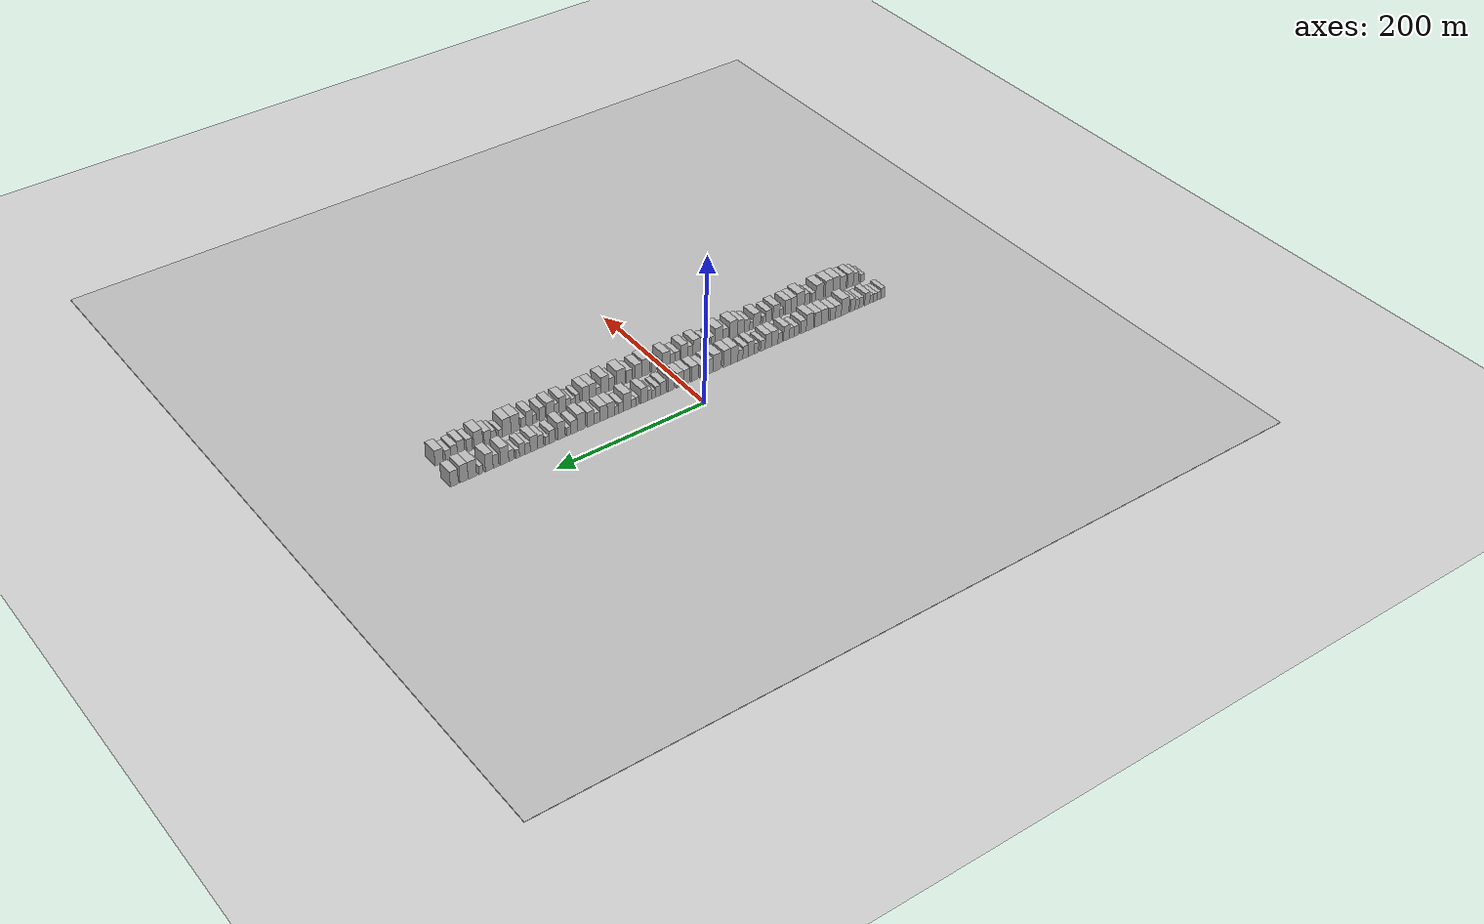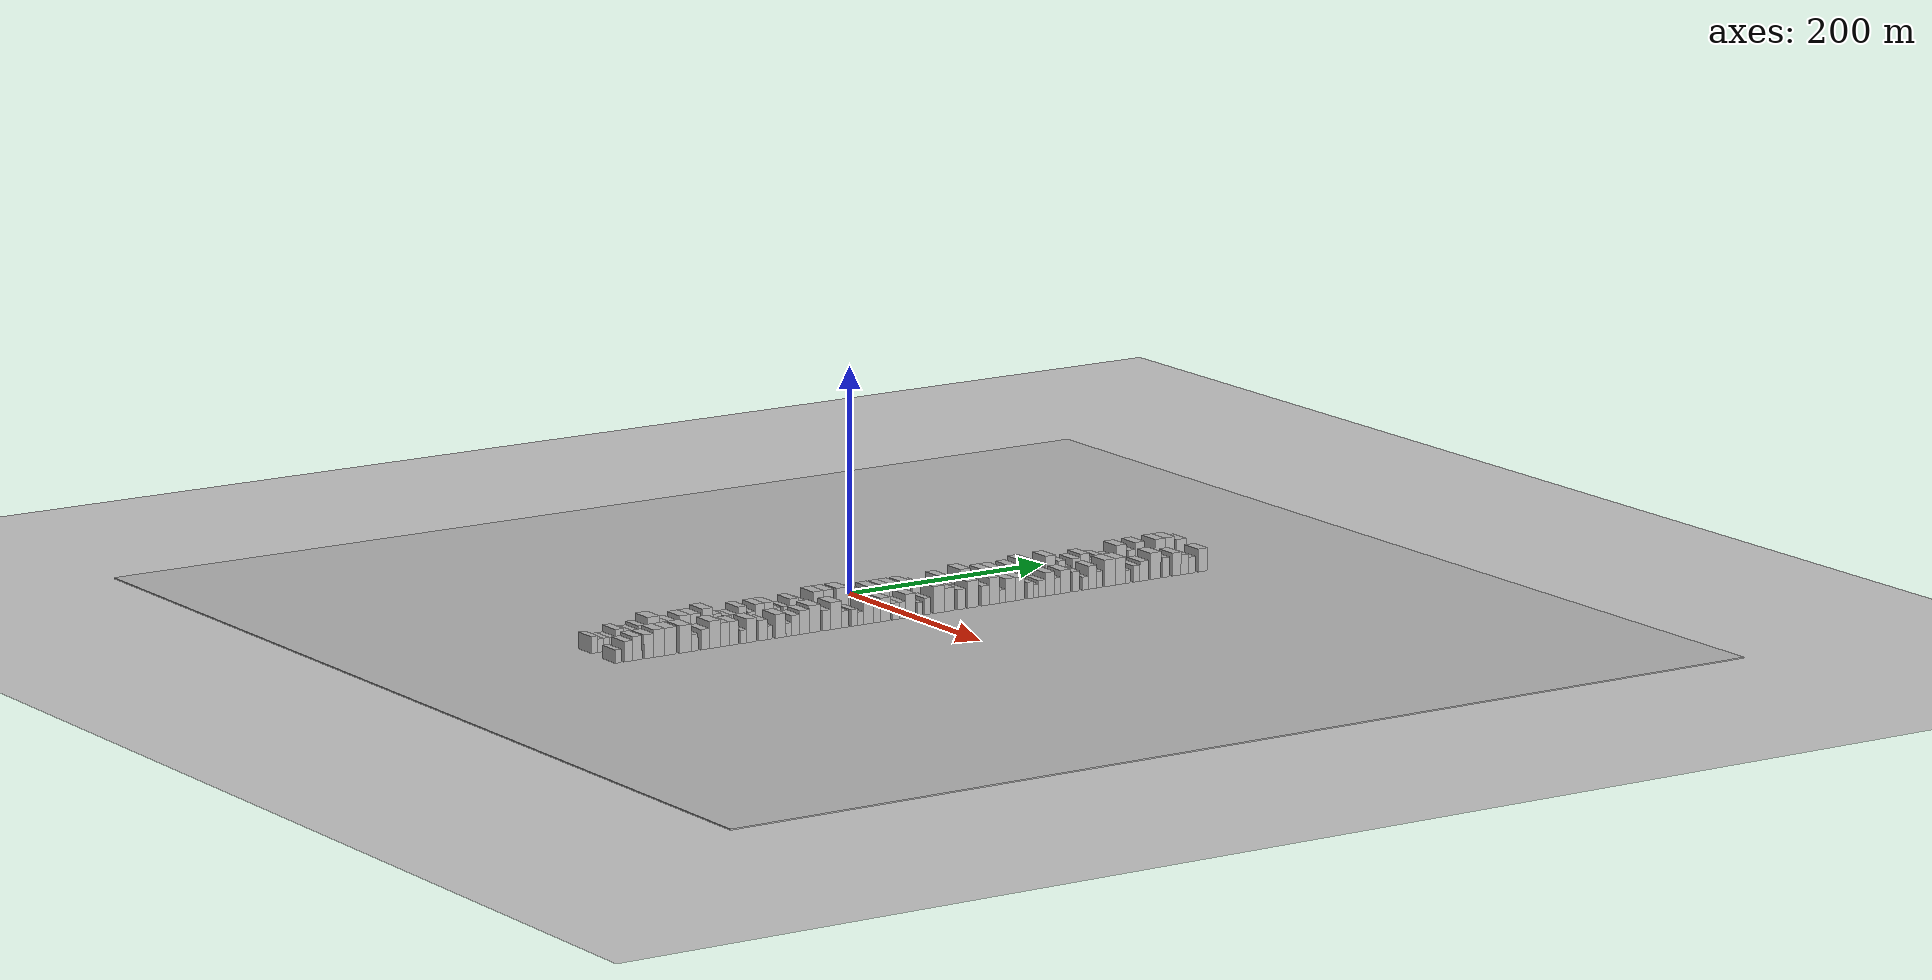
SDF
<?xml version="1.0" encoding="utf-8"?>

<sdf version="1.6">

   <world name="default">

      <gui fullscreen="0">

         <camera name="user_camera">

            <pose>-15 0 4.57585 0 0 0</pose>

            <view_controller>orbit</view_controller>

         </camera>

      </gui>

      <scene>

         <sky>

           <clouds>

             <speed>12</speed>

           </clouds>

         </sky>

         <ambient>0.4 0.4 0.4 1</ambient>

         <background>0.7 0.7 0.7 1</background>

         <shadows>1</shadows>

      </scene>

      <gravity>0 0 -9.8066</gravity>

      <magnetic_field>6e-06 2.3e-05 -4.2e-05</magnetic_field>

      <physics default="0" name="default_physics" type="ode">

         <ode>

            <solver>

               <type>quick</type>

               <iters>10</iters>

               <sor>1.0</sor>

               <use_dynamic_moi_rescaling>0</use_dynamic_moi_rescaling>

            </solver>

            <constraints>

               <cfm>0</cfm>

               <erp>0.2</erp>

               <contact_max_correcting_vel>100</contact_max_correcting_vel>

               <contact_surface_layer>0.001</contact_surface_layer>

            </constraints>

         </ode>

         <max_step_size>0.004</max_step_size>

         <real_time_factor>1</real_time_factor>

         <real_time_update_rate>250</real_time_update_rate>

      </physics>

      <light name="sun" type="directional">

         <cast_shadows>1</cast_shadows>

         <pose>0 0 10 0 0 0</pose>

         <diffuse>0.8 0.8 0.8 1</diffuse>

         <specular>0.2 0.2 0.2 1</specular>

         <attenuation>

            <range>1000</range>

            <constant>0.9</constant>

            <linear>0.01</linear>

            <quadratic>0.001</quadratic>

         </attenuation>

         <direction>-0.5 0.1 -0.9</direction>

      </light>

      <include>

         <name>ground_plane_1</name>

         <uri>model://HANNAS_ground_plane</uri>

         <pose>0 0 0  0 0 0</pose>

      </include>

      <include>

         <name>ground_plane_2</name>

         <uri>model://HANNAS_ground_plane</uri>

         <pose>100 0 0  0 0 0</pose>

      </include>

      <model name="building_1">

         <static>1</static>

         <pose frame="">50.0000 -293.7207 0 0.000000 0.000000 0.000000</pose>

         <link name="link">

            <pose frame="">0 0 7.50 0 0 0</pose>

            <collision name="collision">

               <geometry>

                  <box>

                     <size>20.0000 6.5586 15.0000</size>

                  </box>

               </geometry>

               <max_contacts>10</max_contacts>

               <surface>

                  <contact>

                     <ode/>

                  </contact>

                  <bounce/>

                  <friction>

                     <torsional>

                        <ode/>

                     </torsional>

                     <ode/>

                  </friction>

               </surface>

            </collision>

            <visual name="visual">

               <cast_shadows>0</cast_shadows>

               <geometry>

                  <box>

                     <size>20.0000 6.5586 15.0000</size>

                  </box>

               </geometry>

               <material>

                  <script>

                     <uri>model://HANNAS_wall/materials/scripts</uri>

                     <uri>model://HANNAS_wall/materials/textures</uri>

                     <name>vrc/HANNAS_wall</name>

                  </script>

               </material>

            </visual>

            <self_collide>0</self_collide>

            <enable_wind>0</enable_wind>

            <kinematic>0</kinematic>

         </link>

      </model>

      <model name="building_2">

         <static>1</static>

         <pose frame="">50.0000 -287.6814 0 0.000000 0.000000 0.000000</pose>

         <link name="link">

            <pose frame="">0 0 6.00 0 0 0</pose>

            <collision name="collision">

               <geometry>

                  <box>

                     <size>20.0000 5.5199 12.0000</size>

                  </box>

               </geometry>

               <max_contacts>10</max_contacts>

               <surface>

                  <contact>

                     <ode/>

                  </contact>

                  <bounce/>

                  <friction>

                     <torsional>

                        <ode/>

                     </torsional>

                     <ode/>

                  </friction>

               </surface>

            </collision>

            <visual name="visual">

               <cast_shadows>0</cast_shadows>

               <geometry>

                  <box>

                     <size>20.0000 5.5199 12.0000</size>

                  </box>

               </geometry>

               <material>

                  <script>

                     <uri>model://HANNAS_wall/materials/scripts</uri>

                     <uri>model://HANNAS_wall/materials/textures</uri>

                     <name>vrc/HANNAS_wall</name>

                  </script>

               </material>

            </visual>

            <self_collide>0</self_collide>

            <enable_wind>0</enable_wind>

            <kinematic>0</kinematic>

         </link>

      </model>

      <model name="building_3">

         <static>1</static>

         <pose frame="">50.0000 -282.0184 0 0.000000 0.000000 0.000000</pose>

         <link name="link">

            <pose frame="">0 0 6.00 0 0 0</pose>

            <collision name="collision">

               <geometry>

                  <box>

                     <size>20.0000 5.8060 12.0000</size>

                  </box>

               </geometry>

               <max_contacts>10</max_contacts>

               <surface>

                  <contact>

                     <ode/>

                  </contact>

                  <bounce/>

                  <friction>

                     <torsional>

                        <ode/>

                     </torsional>

                     <ode/>

                  </friction>

               </surface>

            </collision>

            <visual name="visual">

               <cast_shadows>0</cast_shadows>

               <geometry>

                  <box>

                     <size>20.0000 5.8060 12.0000</size>

                  </box>

               </geometry>

               <material>

                  <script>

                     <uri>model://HANNAS_wall/materials/scripts</uri>

                     <uri>model://HANNAS_wall/materials/textures</uri>

                     <name>vrc/HANNAS_wall</name>

                  </script>

               </material>

            </visual>

            <self_collide>0</self_collide>

            <enable_wind>0</enable_wind>

            <kinematic>0</kinematic>

         </link>

      </model>

      <model name="building_4">

         <static>1</static>

         <pose frame="">50.0000 -276.2854 0 0.000000 0.000000 0.000000</pose>

         <link name="link">

            <pose frame="">0 0 6.00 0 0 0</pose>

            <collision name="collision">

               <geometry>

                  <box>

                     <size>20.0000 5.6601 12.0000</size>

                  </box>

               </geometry>

               <max_contacts>10</max_contacts>

               <surface>

                  <contact>

                     <ode/>

                  </contact>

                  <bounce/>

                  <friction>

                     <torsional>

                        <ode/>

                     </torsional>

                     <ode/>

                  </friction>

               </surface>

            </collision>

            <visual name="visual">

               <cast_shadows>0</cast_shadows>

               <geometry>

                  <box>

                     <size>20.0000 5.6601 12.0000</size>

                  </box>

               </geometry>

               <material>

                  <script>

                     <uri>model://HANNAS_wall/materials/scripts</uri>

                     <uri>model://HANNAS_wall/materials/textures</uri>

                     <name>vrc/HANNAS_wall</name>

                  </script>

               </material>

            </visual>

            <self_collide>0</self_collide>

            <enable_wind>0</enable_wind>

            <kinematic>0</kinematic>

         </link>

      </model>

      <model name="building_5">

         <static>1</static>

         <pose frame="">50.0000 -269.5465 0 0.000000 0.000000 0.000000</pose>

         <link name="link">

            <pose frame="">0 0 9.00 0 0 0</pose>

            <collision name="collision">

               <geometry>

                  <box>

                     <size>20.0000 7.8177 18.0000</size>

                  </box>

               </geometry>

               <max_contacts>10</max_contacts>

               <surface>

                  <contact>

                     <ode/>

                  </contact>

                  <bounce/>

                  <friction>

                     <torsional>

                        <ode/>

                     </torsional>

                     <ode/>

                  </friction>

               </surface>

            </collision>

            <visual name="visual">

               <cast_shadows>0</cast_shadows>

               <geometry>

                  <box>

                     <size>20.0000 7.8177 18.0000</size>

                  </box>

               </geometry>

               <material>

                  <script>

                     <uri>model://HANNAS_wall/materials/scripts</uri>

                     <uri>model://HANNAS_wall/materials/textures</uri>

                     <name>vrc/HANNAS_wall</name>

                  </script>

               </material>

            </visual>

            <self_collide>0</self_collide>

            <enable_wind>0</enable_wind>

            <kinematic>0</kinematic>

         </link>

      </model>

      <model name="building_6">

         <static>1</static>

         <pose frame="">50.0000 -260.2850 0 0.000000 0.000000 0.000000</pose>

         <link name="link">

            <pose frame="">0 0 7.50 0 0 0</pose>

            <collision name="collision">

               <geometry>

                  <box>

                     <size>20.0000 6.7053 15.0000</size>

                  </box>

               </geometry>

               <max_contacts>10</max_contacts>

               <surface>

                  <contact>

                     <ode/>

                  </contact>

                  <bounce/>

                  <friction>

                     <torsional>

                        <ode/>

                     </torsional>

                     <ode/>

                  </friction>

               </surface>

            </collision>

            <visual name="visual">

               <cast_shadows>0</cast_shadows>

               <geometry>

                  <box>

                     <size>20.0000 6.7053 15.0000</size>

                  </box>

               </geometry>

               <material>

                  <script>

                     <uri>model://HANNAS_wall/materials/scripts</uri>

                     <uri>model://HANNAS_wall/materials/textures</uri>

                     <name>vrc/HANNAS_wall</name>

                  </script>

               </material>

            </visual>

            <self_collide>0</self_collide>

            <enable_wind>0</enable_wind>

            <kinematic>0</kinematic>

         </link>

      </model>

      <model name="building_7">

         <static>1</static>

         <pose frame="">50.0000 -253.8806 0 0.000000 0.000000 0.000000</pose>

         <link name="link">

            <pose frame="">0 0 7.50 0 0 0</pose>

            <collision name="collision">

               <geometry>

                  <box>

                     <size>20.0000 6.1035 15.0000</size>

                  </box>

               </geometry>

               <max_contacts>10</max_contacts>

               <surface>

                  <contact>

                     <ode/>

                  </contact>

                  <bounce/>

                  <friction>

                     <torsional>

                        <ode/>

                     </torsional>

                     <ode/>

                  </friction>

               </surface>

            </collision>

            <visual name="visual">

               <cast_shadows>0</cast_shadows>

               <geometry>

                  <box>

                     <size>20.0000 6.1035 15.0000</size>

                  </box>

               </geometry>

               <material>

                  <script>

                     <uri>model://HANNAS_wall/materials/scripts</uri>

                     <uri>model://HANNAS_wall/materials/textures</uri>

                     <name>vrc/HANNAS_wall</name>

                  </script>

               </material>

            </visual>

            <self_collide>0</self_collide>

            <enable_wind>0</enable_wind>

            <kinematic>0</kinematic>

         </link>

      </model>

      <model name="building_8">

         <static>1</static>

         <pose frame="">50.0000 -247.1774 0 0.000000 0.000000 0.000000</pose>

         <link name="link">

            <pose frame="">0 0 9.00 0 0 0</pose>

            <collision name="collision">

               <geometry>

                  <box>

                     <size>20.0000 7.3030 18.0000</size>

                  </box>

               </geometry>

               <max_contacts>10</max_contacts>

               <surface>

                  <contact>

                     <ode/>

                  </contact>

                  <bounce/>

                  <friction>

                     <torsional>

                        <ode/>

                     </torsional>

                     <ode/>

                  </friction>

               </surface>

            </collision>

            <visual name="visual">

               <cast_shadows>0</cast_shadows>

               <geometry>

                  <box>

                     <size>20.0000 7.3030 18.0000</size>

                  </box>

               </geometry>

               <material>

                  <script>

                     <uri>model://HANNAS_wall/materials/scripts</uri>

                     <uri>model://HANNAS_wall/materials/textures</uri>

                     <name>vrc/HANNAS_wall</name>

                  </script>

               </material>

            </visual>

            <self_collide>0</self_collide>

            <enable_wind>0</enable_wind>

            <kinematic>0</kinematic>

         </link>

      </model>

      <model name="building_9">

         <static>1</static>

         <pose frame="">50.0000 -235.6194 0 0.000000 0.000000 0.000000</pose>

         <link name="link">

            <pose frame="">0 0 12.00 0 0 0</pose>

            <collision name="collision">

               <geometry>

                  <box>

                     <size>20.0000 11.8131 24.0000</size>

                  </box>

               </geometry>

               <max_contacts>10</max_contacts>

               <surface>

                  <contact>

                     <ode/>

                  </contact>

                  <bounce/>

                  <friction>

                     <torsional>

                        <ode/>

                     </torsional>

                     <ode/>

                  </friction>

               </surface>

            </collision>

            <visual name="visual">

               <cast_shadows>0</cast_shadows>

               <geometry>

                  <box>

                     <size>20.0000 11.8131 24.0000</size>

                  </box>

               </geometry>

               <material>

                  <script>

                     <uri>model://HANNAS_wall/materials/scripts</uri>

                     <uri>model://HANNAS_wall/materials/textures</uri>

                     <name>vrc/HANNAS_wall</name>

                  </script>

               </material>

            </visual>

            <self_collide>0</self_collide>

            <enable_wind>0</enable_wind>

            <kinematic>0</kinematic>

         </link>

      </model>

      <model name="building_10">

         <static>1</static>

         <pose frame="">50.0000 -225.2220 0 0.000000 0.000000 0.000000</pose>

         <link name="link">

            <pose frame="">0 0 9.00 0 0 0</pose>

            <collision name="collision">

               <geometry>

                  <box>

                     <size>20.0000 8.9816 18.0000</size>

                  </box>

               </geometry>

               <max_contacts>10</max_contacts>

               <surface>

                  <contact>

                     <ode/>

                  </contact>

                  <bounce/>

                  <friction>

                     <torsional>

                        <ode/>

                     </torsional>

                     <ode/>

                  </friction>

               </surface>

            </collision>

            <visual name="visual">

               <cast_shadows>0</cast_shadows>

               <geometry>

                  <box>

                     <size>20.0000 8.9816 18.0000</size>

                  </box>

               </geometry>

               <material>

                  <script>

                     <uri>model://HANNAS_wall/materials/scripts</uri>

                     <uri>model://HANNAS_wall/materials/textures</uri>

                     <name>vrc/HANNAS_wall</name>

                  </script>

               </material>

            </visual>

            <self_collide>0</self_collide>

            <enable_wind>0</enable_wind>

            <kinematic>0</kinematic>

         </link>

      </model>

      <model name="building_11">

         <static>1</static>

         <pose frame="">50.0000 -216.6811 0 0.000000 0.000000 0.000000</pose>

         <link name="link">

            <pose frame="">0 0 9.00 0 0 0</pose>

            <collision name="collision">

               <geometry>

                  <box>

                     <size>20.0000 8.1002 18.0000</size>

                  </box>

               </geometry>

               <max_contacts>10</max_contacts>

               <surface>

                  <contact>

                     <ode/>

                  </contact>

                  <bounce/>

                  <friction>

                     <torsional>

                        <ode/>

                     </torsional>

                     <ode/>

                  </friction>

               </surface>

            </collision>

            <visual name="visual">

               <cast_shadows>0</cast_shadows>

               <geometry>

                  <box>

                     <size>20.0000 8.1002 18.0000</size>

                  </box>

               </geometry>

               <material>

                  <script>

                     <uri>model://HANNAS_wall/materials/scripts</uri>

                     <uri>model://HANNAS_wall/materials/textures</uri>

                     <name>vrc/HANNAS_wall</name>

                  </script>

               </material>

            </visual>

            <self_collide>0</self_collide>

            <enable_wind>0</enable_wind>

            <kinematic>0</kinematic>

         </link>

      </model>

      <model name="building_12">

         <static>1</static>

         <pose frame="">50.0000 -204.4950 0 0.000000 0.000000 0.000000</pose>

         <link name="link">

            <pose frame="">0 0 10.50 0 0 0</pose>

            <collision name="collision">

               <geometry>

                  <box>

                     <size>20.0000 10.2720 21.0000</size>

                  </box>

               </geometry>

               <max_contacts>10</max_contacts>

               <surface>

                  <contact>

                     <ode/>

                  </contact>

                  <bounce/>

                  <friction>

                     <torsional>

                        <ode/>

                     </torsional>

                     <ode/>

                  </friction>

               </surface>

            </collision>

            <visual name="visual">

               <cast_shadows>0</cast_shadows>

               <geometry>

                  <box>

                     <size>20.0000 10.2720 21.0000</size>

                  </box>

               </geometry>

               <material>

                  <script>

                     <uri>model://HANNAS_wall/materials/scripts</uri>

                     <uri>model://HANNAS_wall/materials/textures</uri>

                     <name>vrc/HANNAS_wall</name>

                  </script>

               </material>

            </visual>

            <self_collide>0</self_collide>

            <enable_wind>0</enable_wind>

            <kinematic>0</kinematic>

         </link>

      </model>

      <model name="building_13">

         <static>1</static>

         <pose frame="">50.0000 -194.3998 0 0.000000 0.000000 0.000000</pose>

         <link name="link">

            <pose frame="">0 0 10.50 0 0 0</pose>

            <collision name="collision">

               <geometry>

                  <box>

                     <size>20.0000 9.9184 21.0000</size>

                  </box>

               </geometry>

               <max_contacts>10</max_contacts>

               <surface>

                  <contact>

                     <ode/>

                  </contact>

                  <bounce/>

                  <friction>

                     <torsional>

                        <ode/>

                     </torsional>

                     <ode/>

                  </friction>

               </surface>

            </collision>

            <visual name="visual">

               <cast_shadows>0</cast_shadows>

               <geometry>

                  <box>

                     <size>20.0000 9.9184 21.0000</size>

                  </box>

               </geometry>

               <material>

                  <script>

                     <uri>model://HANNAS_wall/materials/scripts</uri>

                     <uri>model://HANNAS_wall/materials/textures</uri>

                     <name>vrc/HANNAS_wall</name>

                  </script>

               </material>

            </visual>

            <self_collide>0</self_collide>

            <enable_wind>0</enable_wind>

            <kinematic>0</kinematic>

         </link>

      </model>

      <model name="building_14">

         <static>1</static>

         <pose frame="">50.0000 -182.0912 0 0.000000 0.000000 0.000000</pose>

         <link name="link">

            <pose frame="">0 0 12.00 0 0 0</pose>

            <collision name="collision">

               <geometry>

                  <box>

                     <size>20.0000 10.6989 24.0000</size>

                  </box>

               </geometry>

               <max_contacts>10</max_contacts>

               <surface>

                  <contact>

                     <ode/>

                  </contact>

                  <bounce/>

                  <friction>

                     <torsional>

                        <ode/>

                     </torsional>

                     <ode/>

                  </friction>

               </surface>

            </collision>

            <visual name="visual">

               <cast_shadows>0</cast_shadows>

               <geometry>

                  <box>

                     <size>20.0000 10.6989 24.0000</size>

                  </box>

               </geometry>

               <material>

                  <script>

                     <uri>model://HANNAS_wall/materials/scripts</uri>

                     <uri>model://HANNAS_wall/materials/textures</uri>

                     <name>vrc/HANNAS_wall</name>

                  </script>

               </material>

            </visual>

            <self_collide>0</self_collide>

            <enable_wind>0</enable_wind>

            <kinematic>0</kinematic>

         </link>

      </model>

      <model name="building_15">

         <static>1</static>

         <pose frame="">50.0000 -172.4970 0 0.000000 0.000000 0.000000</pose>

         <link name="link">

            <pose frame="">0 0 9.00 0 0 0</pose>

            <collision name="collision">

               <geometry>

                  <box>

                     <size>20.0000 8.4894 18.0000</size>

                  </box>

               </geometry>

               <max_contacts>10</max_contacts>

               <surface>

                  <contact>

                     <ode/>

                  </contact>

                  <bounce/>

                  <friction>

                     <torsional>

                        <ode/>

                     </torsional>

                     <ode/>

                  </friction>

               </surface>

            </collision>

            <visual name="visual">

               <cast_shadows>0</cast_shadows>

               <geometry>

                  <box>

                     <size>20.0000 8.4894 18.0000</size>

                  </box>

               </geometry>

               <material>

                  <script>

                     <uri>model://HANNAS_wall/materials/scripts</uri>

                     <uri>model://HANNAS_wall/materials/textures</uri>

                     <name>vrc/HANNAS_wall</name>

                  </script>

               </material>

            </visual>

            <self_collide>0</self_collide>

            <enable_wind>0</enable_wind>

            <kinematic>0</kinematic>

         </link>

      </model>

      <model name="building_16">

         <static>1</static>

         <pose frame="">50.0000 -161.8119 0 0.000000 0.000000 0.000000</pose>

         <link name="link">

            <pose frame="">0 0 7.50 0 0 0</pose>

            <collision name="collision">

               <geometry>

                  <box>

                     <size>20.0000 6.8809 15.0000</size>

                  </box>

               </geometry>

               <max_contacts>10</max_contacts>

               <surface>

                  <contact>

                     <ode/>

                  </contact>

                  <bounce/>

                  <friction>

                     <torsional>

                        <ode/>

                     </torsional>

                     <ode/>

                  </friction>

               </surface>

            </collision>

            <visual name="visual">

               <cast_shadows>0</cast_shadows>

               <geometry>

                  <box>

                     <size>20.0000 6.8809 15.0000</size>

                  </box>

               </geometry>

               <material>

                  <script>

                     <uri>model://HANNAS_wall/materials/scripts</uri>

                     <uri>model://HANNAS_wall/materials/textures</uri>

                     <name>vrc/HANNAS_wall</name>

                  </script>

               </material>

            </visual>

            <self_collide>0</self_collide>

            <enable_wind>0</enable_wind>

            <kinematic>0</kinematic>

         </link>

      </model>

      <model name="building_17">

         <static>1</static>

         <pose frame="">50.0000 -155.0350 0 0.000000 0.000000 0.000000</pose>

         <link name="link">

            <pose frame="">0 0 7.50 0 0 0</pose>

            <collision name="collision">

               <geometry>

                  <box>

                     <size>20.0000 6.6728 15.0000</size>

                  </box>

               </geometry>

               <max_contacts>10</max_contacts>

               <surface>

                  <contact>

                     <ode/>

                  </contact>

                  <bounce/>

                  <friction>

                     <torsional>

                        <ode/>

                     </torsional>

                     <ode/>

                  </friction>

               </surface>

            </collision>

            <visual name="visual">

               <cast_shadows>0</cast_shadows>

               <geometry>

                  <box>

                     <size>20.0000 6.6728 15.0000</size>

                  </box>

               </geometry>

               <material>

                  <script>

                     <uri>model://HANNAS_wall/materials/scripts</uri>

                     <uri>model://HANNAS_wall/materials/textures</uri>

                     <name>vrc/HANNAS_wall</name>

                  </script>

               </material>

            </visual>

            <self_collide>0</self_collide>

            <enable_wind>0</enable_wind>

            <kinematic>0</kinematic>

         </link>

      </model>

      <model name="building_18">

         <static>1</static>

         <pose frame="">50.0000 -147.3848 0 0.000000 0.000000 0.000000</pose>

         <link name="link">

            <pose frame="">0 0 10.50 0 0 0</pose>

            <collision name="collision">

               <geometry>

                  <box>

                     <size>20.0000 8.6277 21.0000</size>

                  </box>

               </geometry>

               <max_contacts>10</max_contacts>

               <surface>

                  <contact>

                     <ode/>

                  </contact>

                  <bounce/>

                  <friction>

                     <torsional>

                        <ode/>

                     </torsional>

                     <ode/>

                  </friction>

               </surface>

            </collision>

            <visual name="visual">

               <cast_shadows>0</cast_shadows>

               <geometry>

                  <box>

                     <size>20.0000 8.6277 21.0000</size>

                  </box>

               </geometry>

               <material>

                  <script>

                     <uri>model://HANNAS_wall/materials/scripts</uri>

                     <uri>model://HANNAS_wall/materials/textures</uri>

                     <name>vrc/HANNAS_wall</name>

                  </script>

               </material>

            </visual>

            <self_collide>0</self_collide>

            <enable_wind>0</enable_wind>

            <kinematic>0</kinematic>

         </link>

      </model>

      <model name="building_19">

         <static>1</static>

         <pose frame="">50.0000 -137.8836 0 0.000000 0.000000 0.000000</pose>

         <link name="link">

            <pose frame="">0 0 7.50 0 0 0</pose>

            <collision name="collision">

               <geometry>

                  <box>

                     <size>20.0000 6.3746 15.0000</size>

                  </box>

               </geometry>

               <max_contacts>10</max_contacts>

               <surface>

                  <contact>

                     <ode/>

                  </contact>

                  <bounce/>

                  <friction>

                     <torsional>

                        <ode/>

                     </torsional>

                     <ode/>

                  </friction>

               </surface>

            </collision>

            <visual name="visual">

               <cast_shadows>0</cast_shadows>

               <geometry>

                  <box>

                     <size>20.0000 6.3746 15.0000</size>

                  </box>

               </geometry>

               <material>

                  <script>

                     <uri>model://HANNAS_wall/materials/scripts</uri>

                     <uri>model://HANNAS_wall/materials/textures</uri>

                     <name>vrc/HANNAS_wall</name>

                  </script>

               </material>

            </visual>

            <self_collide>0</self_collide>

            <enable_wind>0</enable_wind>

            <kinematic>0</kinematic>

         </link>

      </model>

      <model name="building_20">

         <static>1</static>

         <pose frame="">50.0000 -129.8933 0 0.000000 0.000000 0.000000</pose>

         <link name="link">

            <pose frame="">0 0 10.50 0 0 0</pose>

            <collision name="collision">

               <geometry>

                  <box>

                     <size>20.0000 9.6060 21.0000</size>

                  </box>

               </geometry>

               <max_contacts>10</max_contacts>

               <surface>

                  <contact>

                     <ode/>

                  </contact>

                  <bounce/>

                  <friction>

                     <torsional>

                        <ode/>

                     </torsional>

                     <ode/>

                  </friction>

               </surface>

            </collision>

            <visual name="visual">

               <cast_shadows>0</cast_shadows>

               <geometry>

                  <box>

                     <size>20.0000 9.6060 21.0000</size>

                  </box>

               </geometry>

               <material>

                  <script>

                     <uri>model://HANNAS_wall/materials/scripts</uri>

                     <uri>model://HANNAS_wall/materials/textures</uri>

                     <name>vrc/HANNAS_wall</name>

                  </script>

               </material>

            </visual>

            <self_collide>0</self_collide>

            <enable_wind>0</enable_wind>

            <kinematic>0</kinematic>

         </link>

      </model>

      <model name="building_21">

         <static>1</static>

         <pose frame="">50.0000 -120.5425 0 0.000000 0.000000 0.000000</pose>

         <link name="link">

            <pose frame="">0 0 10.50 0 0 0</pose>

            <collision name="collision">

               <geometry>

                  <box>

                     <size>20.0000 9.0956 21.0000</size>

                  </box>

               </geometry>

               <max_contacts>10</max_contacts>

               <surface>

                  <contact>

                     <ode/>

                  </contact>

                  <bounce/>

                  <friction>

                     <torsional>

                        <ode/>

                     </torsional>

                     <ode/>

                  </friction>

               </surface>

            </collision>

            <visual name="visual">

               <cast_shadows>0</cast_shadows>

               <geometry>

                  <box>

                     <size>20.0000 9.0956 21.0000</size>

                  </box>

               </geometry>

               <material>

                  <script>

                     <uri>model://HANNAS_wall/materials/scripts</uri>

                     <uri>model://HANNAS_wall/materials/textures</uri>

                     <name>vrc/HANNAS_wall</name>

                  </script>

               </material>

            </visual>

            <self_collide>0</self_collide>

            <enable_wind>0</enable_wind>

            <kinematic>0</kinematic>

         </link>

      </model>

      <model name="building_22">

         <static>1</static>

         <pose frame="">50.0000 -112.5203 0 0.000000 0.000000 0.000000</pose>

         <link name="link">

            <pose frame="">0 0 7.50 0 0 0</pose>

            <collision name="collision">

               <geometry>

                  <box>

                     <size>20.0000 6.9490 15.0000</size>

                  </box>

               </geometry>

               <max_contacts>10</max_contacts>

               <surface>

                  <contact>

                     <ode/>

                  </contact>

                  <bounce/>

                  <friction>

                     <torsional>

                        <ode/>

                     </torsional>

                     <ode/>

                  </friction>

               </surface>

            </collision>

            <visual name="visual">

               <cast_shadows>0</cast_shadows>

               <geometry>

                  <box>

                     <size>20.0000 6.9490 15.0000</size>

                  </box>

               </geometry>

               <material>

                  <script>

                     <uri>model://HANNAS_wall/materials/scripts</uri>

                     <uri>model://HANNAS_wall/materials/textures</uri>

                     <name>vrc/HANNAS_wall</name>

                  </script>

               </material>

            </visual>

            <self_collide>0</self_collide>

            <enable_wind>0</enable_wind>

            <kinematic>0</kinematic>

         </link>

      </model>

      <model name="building_23">

         <static>1</static>

         <pose frame="">50.0000 -102.9059 0 0.000000 0.000000 0.000000</pose>

         <link name="link">

            <pose frame="">0 0 7.50 0 0 0</pose>

            <collision name="collision">

               <geometry>

                  <box>

                     <size>20.0000 6.2797 15.0000</size>

                  </box>

               </geometry>

               <max_contacts>10</max_contacts>

               <surface>

                  <contact>

                     <ode/>

                  </contact>

                  <bounce/>

                  <friction>

                     <torsional>

                        <ode/>

                     </torsional>

                     <ode/>

                  </friction>

               </surface>

            </collision>

            <visual name="visual">

               <cast_shadows>0</cast_shadows>

               <geometry>

                  <box>

                     <size>20.0000 6.2797 15.0000</size>

                  </box>

               </geometry>

               <material>

                  <script>

                     <uri>model://HANNAS_wall/materials/scripts</uri>

                     <uri>model://HANNAS_wall/materials/textures</uri>

                     <name>vrc/HANNAS_wall</name>

                  </script>

               </material>

            </visual>

            <self_collide>0</self_collide>

            <enable_wind>0</enable_wind>

            <kinematic>0</kinematic>

         </link>

      </model>

      <model name="building_24">

         <static>1</static>

         <pose frame="">50.0000 -95.5656 0 0.000000 0.000000 0.000000</pose>

         <link name="link">

            <pose frame="">0 0 10.50 0 0 0</pose>

            <collision name="collision">

               <geometry>

                  <box>

                     <size>20.0000 8.4011 21.0000</size>

                  </box>

               </geometry>

               <max_contacts>10</max_contacts>

               <surface>

                  <contact>

                     <ode/>

                  </contact>

                  <bounce/>

                  <friction>

                     <torsional>

                        <ode/>

                     </torsional>

                     <ode/>

                  </friction>

               </surface>

            </collision>

            <visual name="visual">

               <cast_shadows>0</cast_shadows>

               <geometry>

                  <box>

                     <size>20.0000 8.4011 21.0000</size>

                  </box>

               </geometry>

               <material>

                  <script>

                     <uri>model://HANNAS_wall/materials/scripts</uri>

                     <uri>model://HANNAS_wall/materials/textures</uri>

                     <name>vrc/HANNAS_wall</name>

                  </script>

               </material>

            </visual>

            <self_collide>0</self_collide>

            <enable_wind>0</enable_wind>

            <kinematic>0</kinematic>

         </link>

      </model>

      <model name="building_25">

         <static>1</static>

         <pose frame="">50.0000 -87.3929 0 0.000000 0.000000 0.000000</pose>

         <link name="link">

            <pose frame="">0 0 9.00 0 0 0</pose>

            <collision name="collision">

               <geometry>

                  <box>

                     <size>20.0000 7.9442 18.0000</size>

                  </box>

               </geometry>

               <max_contacts>10</max_contacts>

               <surface>

                  <contact>

                     <ode/>

                  </contact>

                  <bounce/>

                  <friction>

                     <torsional>

                        <ode/>

                     </torsional>

                     <ode/>

                  </friction>

               </surface>

            </collision>

            <visual name="visual">

               <cast_shadows>0</cast_shadows>

               <geometry>

                  <box>

                     <size>20.0000 7.9442 18.0000</size>

                  </box>

               </geometry>

               <material>

                  <script>

                     <uri>model://HANNAS_wall/materials/scripts</uri>

                     <uri>model://HANNAS_wall/materials/textures</uri>

                     <name>vrc/HANNAS_wall</name>

                  </script>

               </material>

            </visual>

            <self_collide>0</self_collide>

            <enable_wind>0</enable_wind>

            <kinematic>0</kinematic>

         </link>

      </model>

      <model name="building_26">

         <static>1</static>

         <pose frame="">50.0000 -79.8301 0 0.000000 0.000000 0.000000</pose>

         <link name="link">

            <pose frame="">0 0 7.50 0 0 0</pose>

            <collision name="collision">

               <geometry>

                  <box>

                     <size>20.0000 7.1815 15.0000</size>

                  </box>

               </geometry>

               <max_contacts>10</max_contacts>

               <surface>

                  <contact>

                     <ode/>

                  </contact>

                  <bounce/>

                  <friction>

                     <torsional>

                        <ode/>

                     </torsional>

                     <ode/>

                  </friction>

               </surface>

            </collision>

            <visual name="visual">

               <cast_shadows>0</cast_shadows>

               <geometry>

                  <box>

                     <size>20.0000 7.1815 15.0000</size>

                  </box>

               </geometry>

               <material>

                  <script>

                     <uri>model://HANNAS_wall/materials/scripts</uri>

                     <uri>model://HANNAS_wall/materials/textures</uri>

                     <name>vrc/HANNAS_wall</name>

                  </script>

               </material>

            </visual>

            <self_collide>0</self_collide>

            <enable_wind>0</enable_wind>

            <kinematic>0</kinematic>

         </link>

      </model>

      <model name="building_27">

         <static>1</static>

         <pose frame="">50.0000 -70.8516 0 0.000000 0.000000 0.000000</pose>

         <link name="link">

            <pose frame="">0 0 12.00 0 0 0</pose>

            <collision name="collision">

               <geometry>

                  <box>

                     <size>20.0000 10.7755 24.0000</size>

                  </box>

               </geometry>

               <max_contacts>10</max_contacts>

               <surface>

                  <contact>

                     <ode/>

                  </contact>

                  <bounce/>

                  <friction>

                     <torsional>

                        <ode/>

                     </torsional>

                     <ode/>

                  </friction>

               </surface>

            </collision>

            <visual name="visual">

               <cast_shadows>0</cast_shadows>

               <geometry>

                  <box>

                     <size>20.0000 10.7755 24.0000</size>

                  </box>

               </geometry>

               <material>

                  <script>

                     <uri>model://HANNAS_wall/materials/scripts</uri>

                     <uri>model://HANNAS_wall/materials/textures</uri>

                     <name>vrc/HANNAS_wall</name>

                  </script>

               </material>

            </visual>

            <self_collide>0</self_collide>

            <enable_wind>0</enable_wind>

            <kinematic>0</kinematic>

         </link>

      </model>

      <model name="building_28">

         <static>1</static>

         <pose frame="">50.0000 -60.4129 0 0.000000 0.000000 0.000000</pose>

         <link name="link">

            <pose frame="">0 0 12.00 0 0 0</pose>

            <collision name="collision">

               <geometry>

                  <box>

                     <size>20.0000 10.1017 24.0000</size>

                  </box>

               </geometry>

               <max_contacts>10</max_contacts>

               <surface>

                  <contact>

                     <ode/>

                  </contact>

                  <bounce/>

                  <friction>

                     <torsional>

                        <ode/>

                     </torsional>

                     <ode/>

                  </friction>

               </surface>

            </collision>

            <visual name="visual">

               <cast_shadows>0</cast_shadows>

               <geometry>

                  <box>

                     <size>20.0000 10.1017 24.0000</size>

                  </box>

               </geometry>

               <material>

                  <script>

                     <uri>model://HANNAS_wall/materials/scripts</uri>

                     <uri>model://HANNAS_wall/materials/textures</uri>

                     <name>vrc/HANNAS_wall</name>

                  </script>

               </material>

            </visual>

            <self_collide>0</self_collide>

            <enable_wind>0</enable_wind>

            <kinematic>0</kinematic>

         </link>

      </model>

      <model name="building_29">

         <static>1</static>

         <pose frame="">50.0000 -46.5263 0 0.000000 0.000000 0.000000</pose>

         <link name="link">

            <pose frame="">0 0 12.00 0 0 0</pose>

            <collision name="collision">

               <geometry>

                  <box>

                     <size>20.0000 11.6716 24.0000</size>

                  </box>

               </geometry>

               <max_contacts>10</max_contacts>

               <surface>

                  <contact>

                     <ode/>

                  </contact>

                  <bounce/>

                  <friction>

                     <torsional>

                        <ode/>

                     </torsional>

                     <ode/>

                  </friction>

               </surface>

            </collision>

            <visual name="visual">

               <cast_shadows>0</cast_shadows>

               <geometry>

                  <box>

                     <size>20.0000 11.6716 24.0000</size>

                  </box>

               </geometry>

               <material>

                  <script>

                     <uri>model://HANNAS_wall/materials/scripts</uri>

                     <uri>model://HANNAS_wall/materials/textures</uri>

                     <name>vrc/HANNAS_wall</name>

                  </script>

               </material>

            </visual>

            <self_collide>0</self_collide>

            <enable_wind>0</enable_wind>

            <kinematic>0</kinematic>

         </link>

      </model>

      <model name="building_30">

         <static>1</static>

         <pose frame="">50.0000 -35.5764 0 0.000000 0.000000 0.000000</pose>

         <link name="link">

            <pose frame="">0 0 10.50 0 0 0</pose>

            <collision name="collision">

               <geometry>

                  <box>

                     <size>20.0000 10.2283 21.0000</size>

                  </box>

               </geometry>

               <max_contacts>10</max_contacts>

               <surface>

                  <contact>

                     <ode/>

                  </contact>

                  <bounce/>

                  <friction>

                     <torsional>

                        <ode/>

                     </torsional>

                     <ode/>

                  </friction>

               </surface>

            </collision>

            <visual name="visual">

               <cast_shadows>0</cast_shadows>

               <geometry>

                  <box>

                     <size>20.0000 10.2283 21.0000</size>

                  </box>

               </geometry>

               <material>

                  <script>

                     <uri>model://HANNAS_wall/materials/scripts</uri>

                     <uri>model://HANNAS_wall/materials/textures</uri>

                     <name>vrc/HANNAS_wall</name>

                  </script>

               </material>

            </visual>

            <self_collide>0</self_collide>

            <enable_wind>0</enable_wind>

            <kinematic>0</kinematic>

         </link>

      </model>

      <model name="building_31">

         <static>1</static>

         <pose frame="">50.0000 -26.2525 0 0.000000 0.000000 0.000000</pose>

         <link name="link">

            <pose frame="">0 0 9.00 0 0 0</pose>

            <collision name="collision">

               <geometry>

                  <box>

                     <size>20.0000 8.4193 18.0000</size>

                  </box>

               </geometry>

               <max_contacts>10</max_contacts>

               <surface>

                  <contact>

                     <ode/>

                  </contact>

                  <bounce/>

                  <friction>

                     <torsional>

                        <ode/>

                     </torsional>

                     <ode/>

                  </friction>

               </surface>

            </collision>

            <visual name="visual">

               <cast_shadows>0</cast_shadows>

               <geometry>

                  <box>

                     <size>20.0000 8.4193 18.0000</size>

                  </box>

               </geometry>

               <material>

                  <script>

                     <uri>model://HANNAS_wall/materials/scripts</uri>

                     <uri>model://HANNAS_wall/materials/textures</uri>

                     <name>vrc/HANNAS_wall</name>

                  </script>

               </material>

            </visual>

            <self_collide>0</self_collide>

            <enable_wind>0</enable_wind>

            <kinematic>0</kinematic>

         </link>

      </model>

      <model name="building_32">

         <static>1</static>

         <pose frame="">50.0000 -14.8078 0 0.000000 0.000000 0.000000</pose>

         <link name="link">

            <pose frame="">0 0 10.50 0 0 0</pose>

            <collision name="collision">

               <geometry>

                  <box>

                     <size>20.0000 10.4703 21.0000</size>

                  </box>

               </geometry>

               <max_contacts>10</max_contacts>

               <surface>

                  <contact>

                     <ode/>

                  </contact>

                  <bounce/>

                  <friction>

                     <torsional>

                        <ode/>

                     </torsional>

                     <ode/>

                  </friction>

               </surface>

            </collision>

            <visual name="visual">

               <cast_shadows>0</cast_shadows>

               <geometry>

                  <box>

                     <size>20.0000 10.4703 21.0000</size>

                  </box>

               </geometry>

               <material>

                  <script>

                     <uri>model://HANNAS_wall/materials/scripts</uri>

                     <uri>model://HANNAS_wall/materials/textures</uri>

                     <name>vrc/HANNAS_wall</name>

                  </script>

               </material>

            </visual>

            <self_collide>0</self_collide>

            <enable_wind>0</enable_wind>

            <kinematic>0</kinematic>

         </link>

      </model>

      <model name="building_33">

         <static>1</static>

         <pose frame="">50.0000 -3.1432 0 0.000000 0.000000 0.000000</pose>

         <link name="link">

            <pose frame="">0 0 10.50 0 0 0</pose>

            <collision name="collision">

               <geometry>

                  <box>

                     <size>20.0000 8.8589 21.0000</size>

                  </box>

               </geometry>

               <max_contacts>10</max_contacts>

               <surface>

                  <contact>

                     <ode/>

                  </contact>

                  <bounce/>

                  <friction>

                     <torsional>

                        <ode/>

                     </torsional>

                     <ode/>

                  </friction>

               </surface>

            </collision>

            <visual name="visual">

               <cast_shadows>0</cast_shadows>

               <geometry>

                  <box>

                     <size>20.0000 8.8589 21.0000</size>

                  </box>

               </geometry>

               <material>

                  <script>

                     <uri>model://HANNAS_wall/materials/scripts</uri>

                     <uri>model://HANNAS_wall/materials/textures</uri>

                     <name>vrc/HANNAS_wall</name>

                  </script>

               </material>

            </visual>

            <self_collide>0</self_collide>

            <enable_wind>0</enable_wind>

            <kinematic>0</kinematic>

         </link>

      </model>

      <model name="building_34">

         <static>1</static>

         <pose frame="">50.0000 6.0466 0 0.000000 0.000000 0.000000</pose>

         <link name="link">

            <pose frame="">0 0 10.50 0 0 0</pose>

            <collision name="collision">

               <geometry>

                  <box>

                     <size>20.0000 9.5208 21.0000</size>

                  </box>

               </geometry>

               <max_contacts>10</max_contacts>

               <surface>

                  <contact>

                     <ode/>

                  </contact>

                  <bounce/>

                  <friction>

                     <torsional>

                        <ode/>

                     </torsional>

                     <ode/>

                  </friction>

               </surface>

            </collision>

            <visual name="visual">

               <cast_shadows>0</cast_shadows>

               <geometry>

                  <box>

                     <size>20.0000 9.5208 21.0000</size>

                  </box>

               </geometry>

               <material>

                  <script>

                     <uri>model://HANNAS_wall/materials/scripts</uri>

                     <uri>model://HANNAS_wall/materials/textures</uri>

                     <name>vrc/HANNAS_wall</name>

                  </script>

               </material>

            </visual>

            <self_collide>0</self_collide>

            <enable_wind>0</enable_wind>

            <kinematic>0</kinematic>

         </link>

      </model>

      <model name="building_35">

         <static>1</static>

         <pose frame="">50.0000 18.3578 0 0.000000 0.000000 0.000000</pose>

         <link name="link">

            <pose frame="">0 0 10.50 0 0 0</pose>

            <collision name="collision">

               <geometry>

                  <box>

                     <size>20.0000 9.1016 21.0000</size>

                  </box>

               </geometry>

               <max_contacts>10</max_contacts>

               <surface>

                  <contact>

                     <ode/>

                  </contact>

                  <bounce/>

                  <friction>

                     <torsional>

                        <ode/>

                     </torsional>

                     <ode/>

                  </friction>

               </surface>

            </collision>

            <visual name="visual">

               <cast_shadows>0</cast_shadows>

               <geometry>

                  <box>

                     <size>20.0000 9.1016 21.0000</size>

                  </box>

               </geometry>

               <material>

                  <script>

                     <uri>model://HANNAS_wall/materials/scripts</uri>

                     <uri>model://HANNAS_wall/materials/textures</uri>

                     <name>vrc/HANNAS_wall</name>

                  </script>

               </material>

            </visual>

            <self_collide>0</self_collide>

            <enable_wind>0</enable_wind>

            <kinematic>0</kinematic>

         </link>

      </model>

      <model name="building_36">

         <static>1</static>

         <pose frame="">50.0000 29.3276 0 0.000000 0.000000 0.000000</pose>

         <link name="link">

            <pose frame="">0 0 9.00 0 0 0</pose>

            <collision name="collision">

               <geometry>

                  <box>

                     <size>20.0000 8.8378 18.0000</size>

                  </box>

               </geometry>

               <max_contacts>10</max_contacts>

               <surface>

                  <contact>

                     <ode/>

                  </contact>

                  <bounce/>

                  <friction>

                     <torsional>

                        <ode/>

                     </torsional>

                     <ode/>

                  </friction>

               </surface>

            </collision>

            <visual name="visual">

               <cast_shadows>0</cast_shadows>

               <geometry>

                  <box>

                     <size>20.0000 8.8378 18.0000</size>

                  </box>

               </geometry>

               <material>

                  <script>

                     <uri>model://HANNAS_wall/materials/scripts</uri>

                     <uri>model://HANNAS_wall/materials/textures</uri>

                     <name>vrc/HANNAS_wall</name>

                  </script>

               </material>

            </visual>

            <self_collide>0</self_collide>

            <enable_wind>0</enable_wind>

            <kinematic>0</kinematic>

         </link>

      </model>

      <model name="building_37">

         <static>1</static>

         <pose frame="">50.0000 37.1012 0 0.000000 0.000000 0.000000</pose>

         <link name="link">

            <pose frame="">0 0 7.50 0 0 0</pose>

            <collision name="collision">

               <geometry>

                  <box>

                     <size>20.0000 6.7094 15.0000</size>

                  </box>

               </geometry>

               <max_contacts>10</max_contacts>

               <surface>

                  <contact>

                     <ode/>

                  </contact>

                  <bounce/>

                  <friction>

                     <torsional>

                        <ode/>

                     </torsional>

                     <ode/>

                  </friction>

               </surface>

            </collision>

            <visual name="visual">

               <cast_shadows>0</cast_shadows>

               <geometry>

                  <box>

                     <size>20.0000 6.7094 15.0000</size>

                  </box>

               </geometry>

               <material>

                  <script>

                     <uri>model://HANNAS_wall/materials/scripts</uri>

                     <uri>model://HANNAS_wall/materials/textures</uri>

                     <name>vrc/HANNAS_wall</name>

                  </script>

               </material>

            </visual>

            <self_collide>0</self_collide>

            <enable_wind>0</enable_wind>

            <kinematic>0</kinematic>

         </link>

      </model>

      <model name="building_38">

         <static>1</static>

         <pose frame="">50.0000 42.8789 0 0.000000 0.000000 0.000000</pose>

         <link name="link">

            <pose frame="">0 0 6.00 0 0 0</pose>

            <collision name="collision">

               <geometry>

                  <box>

                     <size>20.0000 4.8460 12.0000</size>

                  </box>

               </geometry>

               <max_contacts>10</max_contacts>

               <surface>

                  <contact>

                     <ode/>

                  </contact>

                  <bounce/>

                  <friction>

                     <torsional>

                        <ode/>

                     </torsional>

                     <ode/>

                  </friction>

               </surface>

            </collision>

            <visual name="visual">

               <cast_shadows>0</cast_shadows>

               <geometry>

                  <box>

                     <size>20.0000 4.8460 12.0000</size>

                  </box>

               </geometry>

               <material>

                  <script>

                     <uri>model://HANNAS_wall/materials/scripts</uri>

                     <uri>model://HANNAS_wall/materials/textures</uri>

                     <name>vrc/HANNAS_wall</name>

                  </script>

               </material>

            </visual>

            <self_collide>0</self_collide>

            <enable_wind>0</enable_wind>

            <kinematic>0</kinematic>

         </link>

      </model>

      <model name="building_39">

         <static>1</static>

         <pose frame="">50.0000 48.4959 0 0.000000 0.000000 0.000000</pose>

         <link name="link">

            <pose frame="">0 0 7.50 0 0 0</pose>

            <collision name="collision">

               <geometry>

                  <box>

                     <size>20.0000 6.3881 15.0000</size>

                  </box>

               </geometry>

               <max_contacts>10</max_contacts>

               <surface>

                  <contact>

                     <ode/>

                  </contact>

                  <bounce/>

                  <friction>

                     <torsional>

                        <ode/>

                     </torsional>

                     <ode/>

                  </friction>

               </surface>

            </collision>

            <visual name="visual">

               <cast_shadows>0</cast_shadows>

               <geometry>

                  <box>

                     <size>20.0000 6.3881 15.0000</size>

                  </box>

               </geometry>

               <material>

                  <script>

                     <uri>model://HANNAS_wall/materials/scripts</uri>

                     <uri>model://HANNAS_wall/materials/textures</uri>

                     <name>vrc/HANNAS_wall</name>

                  </script>

               </material>

            </visual>

            <self_collide>0</self_collide>

            <enable_wind>0</enable_wind>

            <kinematic>0</kinematic>

         </link>

      </model>

      <model name="building_40">

         <static>1</static>

         <pose frame="">50.0000 56.1326 0 0.000000 0.000000 0.000000</pose>

         <link name="link">

            <pose frame="">0 0 10.50 0 0 0</pose>

            <collision name="collision">

               <geometry>

                  <box>

                     <size>20.0000 8.8852 21.0000</size>

                  </box>

               </geometry>

               <max_contacts>10</max_contacts>

               <surface>

                  <contact>

                     <ode/>

                  </contact>

                  <bounce/>

                  <friction>

                     <torsional>

                        <ode/>

                     </torsional>

                     <ode/>

                  </friction>

               </surface>

            </collision>

            <visual name="visual">

               <cast_shadows>0</cast_shadows>

               <geometry>

                  <box>

                     <size>20.0000 8.8852 21.0000</size>

                  </box>

               </geometry>

               <material>

                  <script>

                     <uri>model://HANNAS_wall/materials/scripts</uri>

                     <uri>model://HANNAS_wall/materials/textures</uri>

                     <name>vrc/HANNAS_wall</name>

                  </script>

               </material>

            </visual>

            <self_collide>0</self_collide>

            <enable_wind>0</enable_wind>

            <kinematic>0</kinematic>

         </link>

      </model>

      <model name="building_41">

         <static>1</static>

         <pose frame="">50.0000 65.1850 0 0.000000 0.000000 0.000000</pose>

         <link name="link">

            <pose frame="">0 0 6.00 0 0 0</pose>

            <collision name="collision">

               <geometry>

                  <box>

                     <size>20.0000 5.2195 12.0000</size>

                  </box>

               </geometry>

               <max_contacts>10</max_contacts>

               <surface>

                  <contact>

                     <ode/>

                  </contact>

                  <bounce/>

                  <friction>

                     <torsional>

                        <ode/>

                     </torsional>

                     <ode/>

                  </friction>

               </surface>

            </collision>

            <visual name="visual">

               <cast_shadows>0</cast_shadows>

               <geometry>

                  <box>

                     <size>20.0000 5.2195 12.0000</size>

                  </box>

               </geometry>

               <material>

                  <script>

                     <uri>model://HANNAS_wall/materials/scripts</uri>

                     <uri>model://HANNAS_wall/materials/textures</uri>

                     <name>vrc/HANNAS_wall</name>

                  </script>

               </material>

            </visual>

            <self_collide>0</self_collide>

            <enable_wind>0</enable_wind>

            <kinematic>0</kinematic>

         </link>

      </model>

      <model name="building_42">

         <static>1</static>

         <pose frame="">50.0000 70.6543 0 0.000000 0.000000 0.000000</pose>

         <link name="link">

            <pose frame="">0 0 6.00 0 0 0</pose>

            <collision name="collision">

               <geometry>

                  <box>

                     <size>20.0000 5.7191 12.0000</size>

                  </box>

               </geometry>

               <max_contacts>10</max_contacts>

               <surface>

                  <contact>

                     <ode/>

                  </contact>

                  <bounce/>

                  <friction>

                     <torsional>

                        <ode/>

                     </torsional>

                     <ode/>

                  </friction>

               </surface>

            </collision>

            <visual name="visual">

               <cast_shadows>0</cast_shadows>

               <geometry>

                  <box>

                     <size>20.0000 5.7191 12.0000</size>

                  </box>

               </geometry>

               <material>

                  <script>

                     <uri>model://HANNAS_wall/materials/scripts</uri>

                     <uri>model://HANNAS_wall/materials/textures</uri>

                     <name>vrc/HANNAS_wall</name>

                  </script>

               </material>

            </visual>

            <self_collide>0</self_collide>

            <enable_wind>0</enable_wind>

            <kinematic>0</kinematic>

         </link>

      </model>

      <model name="building_43">

         <static>1</static>

         <pose frame="">50.0000 78.7085 0 0.000000 0.000000 0.000000</pose>

         <link name="link">

            <pose frame="">0 0 12.00 0 0 0</pose>

            <collision name="collision">

               <geometry>

                  <box>

                     <size>20.0000 10.3895 24.0000</size>

                  </box>

               </geometry>

               <max_contacts>10</max_contacts>

               <surface>

                  <contact>

                     <ode/>

                  </contact>

                  <bounce/>

                  <friction>

                     <torsional>

                        <ode/>

                     </torsional>

                     <ode/>

                  </friction>

               </surface>

            </collision>

            <visual name="visual">

               <cast_shadows>0</cast_shadows>

               <geometry>

                  <box>

                     <size>20.0000 10.3895 24.0000</size>

                  </box>

               </geometry>

               <material>

                  <script>

                     <uri>model://HANNAS_wall/materials/scripts</uri>

                     <uri>model://HANNAS_wall/materials/textures</uri>

                     <name>vrc/HANNAS_wall</name>

                  </script>

               </material>

            </visual>

            <self_collide>0</self_collide>

            <enable_wind>0</enable_wind>

            <kinematic>0</kinematic>

         </link>

      </model>

      <model name="building_44">

         <static>1</static>

         <pose frame="">50.0000 87.5398 0 0.000000 0.000000 0.000000</pose>

         <link name="link">

            <pose frame="">0 0 7.50 0 0 0</pose>

            <collision name="collision">

               <geometry>

                  <box>

                     <size>20.0000 7.2731 15.0000</size>

                  </box>

               </geometry>

               <max_contacts>10</max_contacts>

               <surface>

                  <contact>

                     <ode/>

                  </contact>

                  <bounce/>

                  <friction>

                     <torsional>

                        <ode/>

                     </torsional>

                     <ode/>

                  </friction>

               </surface>

            </collision>

            <visual name="visual">

               <cast_shadows>0</cast_shadows>

               <geometry>

                  <box>

                     <size>20.0000 7.2731 15.0000</size>

                  </box>

               </geometry>

               <material>

                  <script>

                     <uri>model://HANNAS_wall/materials/scripts</uri>

                     <uri>model://HANNAS_wall/materials/textures</uri>

                     <name>vrc/HANNAS_wall</name>

                  </script>

               </material>

            </visual>

            <self_collide>0</self_collide>

            <enable_wind>0</enable_wind>

            <kinematic>0</kinematic>

         </link>

      </model>

      <model name="building_45">

         <static>1</static>

         <pose frame="">50.0000 93.7264 0 0.000000 0.000000 0.000000</pose>

         <link name="link">

            <pose frame="">0 0 6.00 0 0 0</pose>

            <collision name="collision">

               <geometry>

                  <box>

                     <size>20.0000 5.1001 12.0000</size>

                  </box>

               </geometry>

               <max_contacts>10</max_contacts>

               <surface>

                  <contact>

                     <ode/>

                  </contact>

                  <bounce/>

                  <friction>

                     <torsional>

                        <ode/>

                     </torsional>

                     <ode/>

                  </friction>

               </surface>

            </collision>

            <visual name="visual">

               <cast_shadows>0</cast_shadows>

               <geometry>

                  <box>

                     <size>20.0000 5.1001 12.0000</size>

                  </box>

               </geometry>

               <material>

                  <script>

                     <uri>model://HANNAS_wall/materials/scripts</uri>

                     <uri>model://HANNAS_wall/materials/textures</uri>

                     <name>vrc/HANNAS_wall</name>

                  </script>

               </material>

            </visual>

            <self_collide>0</self_collide>

            <enable_wind>0</enable_wind>

            <kinematic>0</kinematic>

         </link>

      </model>

      <model name="building_46">

         <static>1</static>

         <pose frame="">50.0000 101.2266 0 0.000000 0.000000 0.000000</pose>

         <link name="link">

            <pose frame="">0 0 10.50 0 0 0</pose>

            <collision name="collision">

               <geometry>

                  <box>

                     <size>20.0000 9.9003 21.0000</size>

                  </box>

               </geometry>

               <max_contacts>10</max_contacts>

               <surface>

                  <contact>

                     <ode/>

                  </contact>

                  <bounce/>

                  <friction>

                     <torsional>

                        <ode/>

                     </torsional>

                     <ode/>

                  </friction>

               </surface>

            </collision>

            <visual name="visual">

               <cast_shadows>0</cast_shadows>

               <geometry>

                  <box>

                     <size>20.0000 9.9003 21.0000</size>

                  </box>

               </geometry>

               <material>

                  <script>

                     <uri>model://HANNAS_wall/materials/scripts</uri>

                     <uri>model://HANNAS_wall/materials/textures</uri>

                     <name>vrc/HANNAS_wall</name>

                  </script>

               </material>

            </visual>

            <self_collide>0</self_collide>

            <enable_wind>0</enable_wind>

            <kinematic>0</kinematic>

         </link>

      </model>

      <model name="building_47">

         <static>1</static>

         <pose frame="">50.0000 111.3244 0 0.000000 0.000000 0.000000</pose>

         <link name="link">

            <pose frame="">0 0 10.50 0 0 0</pose>

            <collision name="collision">

               <geometry>

                  <box>

                     <size>20.0000 10.2953 21.0000</size>

                  </box>

               </geometry>

               <max_contacts>10</max_contacts>

               <surface>

                  <contact>

                     <ode/>

                  </contact>

                  <bounce/>

                  <friction>

                     <torsional>

                        <ode/>

                     </torsional>

                     <ode/>

                  </friction>

               </surface>

            </collision>

            <visual name="visual">

               <cast_shadows>0</cast_shadows>

               <geometry>

                  <box>

                     <size>20.0000 10.2953 21.0000</size>

                  </box>

               </geometry>

               <material>

                  <script>

                     <uri>model://HANNAS_wall/materials/scripts</uri>

                     <uri>model://HANNAS_wall/materials/textures</uri>

                     <name>vrc/HANNAS_wall</name>

                  </script>

               </material>

            </visual>

            <self_collide>0</self_collide>

            <enable_wind>0</enable_wind>

            <kinematic>0</kinematic>

         </link>

      </model>

      <model name="building_48">

         <static>1</static>

         <pose frame="">50.0000 120.0511 0 0.000000 0.000000 0.000000</pose>

         <link name="link">

            <pose frame="">0 0 7.50 0 0 0</pose>

            <collision name="collision">

               <geometry>

                  <box>

                     <size>20.0000 7.1583 15.0000</size>

                  </box>

               </geometry>

               <max_contacts>10</max_contacts>

               <surface>

                  <contact>

                     <ode/>

                  </contact>

                  <bounce/>

                  <friction>

                     <torsional>

                        <ode/>

                     </torsional>

                     <ode/>

                  </friction>

               </surface>

            </collision>

            <visual name="visual">

               <cast_shadows>0</cast_shadows>

               <geometry>

                  <box>

                     <size>20.0000 7.1583 15.0000</size>

                  </box>

               </geometry>

               <material>

                  <script>

                     <uri>model://HANNAS_wall/materials/scripts</uri>

                     <uri>model://HANNAS_wall/materials/textures</uri>

                     <name>vrc/HANNAS_wall</name>

                  </script>

               </material>

            </visual>

            <self_collide>0</self_collide>

            <enable_wind>0</enable_wind>

            <kinematic>0</kinematic>

         </link>

      </model>

      <model name="building_49">

         <static>1</static>

         <pose frame="">50.0000 128.2841 0 0.000000 0.000000 0.000000</pose>

         <link name="link">

            <pose frame="">0 0 10.50 0 0 0</pose>

            <collision name="collision">

               <geometry>

                  <box>

                     <size>20.0000 9.3077 21.0000</size>

                  </box>

               </geometry>

               <max_contacts>10</max_contacts>

               <surface>

                  <contact>

                     <ode/>

                  </contact>

                  <bounce/>

                  <friction>

                     <torsional>

                        <ode/>

                     </torsional>

                     <ode/>

                  </friction>

               </surface>

            </collision>

            <visual name="visual">

               <cast_shadows>0</cast_shadows>

               <geometry>

                  <box>

                     <size>20.0000 9.3077 21.0000</size>

                  </box>

               </geometry>

               <material>

                  <script>

                     <uri>model://HANNAS_wall/materials/scripts</uri>

                     <uri>model://HANNAS_wall/materials/textures</uri>

                     <name>vrc/HANNAS_wall</name>

                  </script>

               </material>

            </visual>

            <self_collide>0</self_collide>

            <enable_wind>0</enable_wind>

            <kinematic>0</kinematic>

         </link>

      </model>

      <model name="building_50">

         <static>1</static>

         <pose frame="">50.0000 141.2554 0 0.000000 0.000000 0.000000</pose>

         <link name="link">

            <pose frame="">0 0 12.00 0 0 0</pose>

            <collision name="collision">

               <geometry>

                  <box>

                     <size>20.0000 10.6349 24.0000</size>

                  </box>

               </geometry>

               <max_contacts>10</max_contacts>

               <surface>

                  <contact>

                     <ode/>

                  </contact>

                  <bounce/>

                  <friction>

                     <torsional>

                        <ode/>

                     </torsional>

                     <ode/>

                  </friction>

               </surface>

            </collision>

            <visual name="visual">

               <cast_shadows>0</cast_shadows>

               <geometry>

                  <box>

                     <size>20.0000 10.6349 24.0000</size>

                  </box>

               </geometry>

               <material>

                  <script>

                     <uri>model://HANNAS_wall/materials/scripts</uri>

                     <uri>model://HANNAS_wall/materials/textures</uri>

                     <name>vrc/HANNAS_wall</name>

                  </script>

               </material>

            </visual>

            <self_collide>0</self_collide>

            <enable_wind>0</enable_wind>

            <kinematic>0</kinematic>

         </link>

      </model>

      <model name="building_51">

         <static>1</static>

         <pose frame="">50.0000 150.9640 0 0.000000 0.000000 0.000000</pose>

         <link name="link">

            <pose frame="">0 0 9.00 0 0 0</pose>

            <collision name="collision">

               <geometry>

                  <box>

                     <size>20.0000 8.7823 18.0000</size>

                  </box>

               </geometry>

               <max_contacts>10</max_contacts>

               <surface>

                  <contact>

                     <ode/>

                  </contact>

                  <bounce/>

                  <friction>

                     <torsional>

                        <ode/>

                     </torsional>

                     <ode/>

                  </friction>

               </surface>

            </collision>

            <visual name="visual">

               <cast_shadows>0</cast_shadows>

               <geometry>

                  <box>

                     <size>20.0000 8.7823 18.0000</size>

                  </box>

               </geometry>

               <material>

                  <script>

                     <uri>model://HANNAS_wall/materials/scripts</uri>

                     <uri>model://HANNAS_wall/materials/textures</uri>

                     <name>vrc/HANNAS_wall</name>

                  </script>

               </material>

            </visual>

            <self_collide>0</self_collide>

            <enable_wind>0</enable_wind>

            <kinematic>0</kinematic>

         </link>

      </model>

      <model name="building_52">

         <static>1</static>

         <pose frame="">50.0000 157.9376 0 0.000000 0.000000 0.000000</pose>

         <link name="link">

            <pose frame="">0 0 6.00 0 0 0</pose>

            <collision name="collision">

               <geometry>

                  <box>

                     <size>20.0000 5.1650 12.0000</size>

                  </box>

               </geometry>

               <max_contacts>10</max_contacts>

               <surface>

                  <contact>

                     <ode/>

                  </contact>

                  <bounce/>

                  <friction>

                     <torsional>

                        <ode/>

                     </torsional>

                     <ode/>

                  </friction>

               </surface>

            </collision>

            <visual name="visual">

               <cast_shadows>0</cast_shadows>

               <geometry>

                  <box>

                     <size>20.0000 5.1650 12.0000</size>

                  </box>

               </geometry>

               <material>

                  <script>

                     <uri>model://HANNAS_wall/materials/scripts</uri>

                     <uri>model://HANNAS_wall/materials/textures</uri>

                     <name>vrc/HANNAS_wall</name>

                  </script>

               </material>

            </visual>

            <self_collide>0</self_collide>

            <enable_wind>0</enable_wind>

            <kinematic>0</kinematic>

         </link>

      </model>

      <model name="building_53">

         <static>1</static>

         <pose frame="">50.0000 167.4618 0 0.000000 0.000000 0.000000</pose>

         <link name="link">

            <pose frame="">0 0 12.00 0 0 0</pose>

            <collision name="collision">

               <geometry>

                  <box>

                     <size>20.0000 9.8834 24.0000</size>

                  </box>

               </geometry>

               <max_contacts>10</max_contacts>

               <surface>

                  <contact>

                     <ode/>

                  </contact>

                  <bounce/>

                  <friction>

                     <torsional>

                        <ode/>

                     </torsional>

                     <ode/>

                  </friction>

               </surface>

            </collision>

            <visual name="visual">

               <cast_shadows>0</cast_shadows>

               <geometry>

                  <box>

                     <size>20.0000 9.8834 24.0000</size>

                  </box>

               </geometry>

               <material>

                  <script>

                     <uri>model://HANNAS_wall/materials/scripts</uri>

                     <uri>model://HANNAS_wall/materials/textures</uri>

                     <name>vrc/HANNAS_wall</name>

                  </script>

               </material>

            </visual>

            <self_collide>0</self_collide>

            <enable_wind>0</enable_wind>

            <kinematic>0</kinematic>

         </link>

      </model>

      <model name="building_54">

         <static>1</static>

         <pose frame="">50.0000 179.4813 0 0.000000 0.000000 0.000000</pose>

         <link name="link">

            <pose frame="">0 0 9.00 0 0 0</pose>

            <collision name="collision">

               <geometry>

                  <box>

                     <size>20.0000 8.1556 18.0000</size>

                  </box>

               </geometry>

               <max_contacts>10</max_contacts>

               <surface>

                  <contact>

                     <ode/>

                  </contact>

                  <bounce/>

                  <friction>

                     <torsional>

                        <ode/>

                     </torsional>

                     <ode/>

                  </friction>

               </surface>

            </collision>

            <visual name="visual">

               <cast_shadows>0</cast_shadows>

               <geometry>

                  <box>

                     <size>20.0000 8.1556 18.0000</size>

                  </box>

               </geometry>

               <material>

                  <script>

                     <uri>model://HANNAS_wall/materials/scripts</uri>

                     <uri>model://HANNAS_wall/materials/textures</uri>

                     <name>vrc/HANNAS_wall</name>

                  </script>

               </material>

            </visual>

            <self_collide>0</self_collide>

            <enable_wind>0</enable_wind>

            <kinematic>0</kinematic>

         </link>

      </model>

      <model name="building_55">

         <static>1</static>

         <pose frame="">50.0000 186.1787 0 0.000000 0.000000 0.000000</pose>

         <link name="link">

            <pose frame="">0 0 6.00 0 0 0</pose>

            <collision name="collision">

               <geometry>

                  <box>

                     <size>20.0000 5.2392 12.0000</size>

                  </box>

               </geometry>

               <max_contacts>10</max_contacts>

               <surface>

                  <contact>

                     <ode/>

                  </contact>

                  <bounce/>

                  <friction>

                     <torsional>

                        <ode/>

                     </torsional>

                     <ode/>

                  </friction>

               </surface>

            </collision>

            <visual name="visual">

               <cast_shadows>0</cast_shadows>

               <geometry>

                  <box>

                     <size>20.0000 5.2392 12.0000</size>

                  </box>

               </geometry>

               <material>

                  <script>

                     <uri>model://HANNAS_wall/materials/scripts</uri>

                     <uri>model://HANNAS_wall/materials/textures</uri>

                     <name>vrc/HANNAS_wall</name>

                  </script>

               </material>

            </visual>

            <self_collide>0</self_collide>

            <enable_wind>0</enable_wind>

            <kinematic>0</kinematic>

         </link>

      </model>

      <model name="building_56">

         <static>1</static>

         <pose frame="">50.0000 194.8588 0 0.000000 0.000000 0.000000</pose>

         <link name="link">

            <pose frame="">0 0 9.00 0 0 0</pose>

            <collision name="collision">

               <geometry>

                  <box>

                     <size>20.0000 8.1209 18.0000</size>

                  </box>

               </geometry>

               <max_contacts>10</max_contacts>

               <surface>

                  <contact>

                     <ode/>

                  </contact>

                  <bounce/>

                  <friction>

                     <torsional>

                        <ode/>

                     </torsional>

                     <ode/>

                  </friction>

               </surface>

            </collision>

            <visual name="visual">

               <cast_shadows>0</cast_shadows>

               <geometry>

                  <box>

                     <size>20.0000 8.1209 18.0000</size>

                  </box>

               </geometry>

               <material>

                  <script>

                     <uri>model://HANNAS_wall/materials/scripts</uri>

                     <uri>model://HANNAS_wall/materials/textures</uri>

                     <name>vrc/HANNAS_wall</name>

                  </script>

               </material>

            </visual>

            <self_collide>0</self_collide>

            <enable_wind>0</enable_wind>

            <kinematic>0</kinematic>

         </link>

      </model>

      <model name="building_57">

         <static>1</static>

         <pose frame="">50.0000 203.6728 0 0.000000 0.000000 0.000000</pose>

         <link name="link">

            <pose frame="">0 0 10.50 0 0 0</pose>

            <collision name="collision">

               <geometry>

                  <box>

                     <size>20.0000 9.5072 21.0000</size>

                  </box>

               </geometry>

               <max_contacts>10</max_contacts>

               <surface>

                  <contact>

                     <ode/>

                  </contact>

                  <bounce/>

                  <friction>

                     <torsional>

                        <ode/>

                     </torsional>

                     <ode/>

                  </friction>

               </surface>

            </collision>

            <visual name="visual">

               <cast_shadows>0</cast_shadows>

               <geometry>

                  <box>

                     <size>20.0000 9.5072 21.0000</size>

                  </box>

               </geometry>

               <material>

                  <script>

                     <uri>model://HANNAS_wall/materials/scripts</uri>

                     <uri>model://HANNAS_wall/materials/textures</uri>

                     <name>vrc/HANNAS_wall</name>

                  </script>

               </material>

            </visual>

            <self_collide>0</self_collide>

            <enable_wind>0</enable_wind>

            <kinematic>0</kinematic>

         </link>

      </model>

      <model name="building_58">

         <static>1</static>

         <pose frame="">50.0000 211.8074 0 0.000000 0.000000 0.000000</pose>

         <link name="link">

            <pose frame="">0 0 7.50 0 0 0</pose>

            <collision name="collision">

               <geometry>

                  <box>

                     <size>20.0000 6.7619 15.0000</size>

                  </box>

               </geometry>

               <max_contacts>10</max_contacts>

               <surface>

                  <contact>

                     <ode/>

                  </contact>

                  <bounce/>

                  <friction>

                     <torsional>

                        <ode/>

                     </torsional>

                     <ode/>

                  </friction>

               </surface>

            </collision>

            <visual name="visual">

               <cast_shadows>0</cast_shadows>

               <geometry>

                  <box>

                     <size>20.0000 6.7619 15.0000</size>

                  </box>

               </geometry>

               <material>

                  <script>

                     <uri>model://HANNAS_wall/materials/scripts</uri>

                     <uri>model://HANNAS_wall/materials/textures</uri>

                     <name>vrc/HANNAS_wall</name>

                  </script>

               </material>

            </visual>

            <self_collide>0</self_collide>

            <enable_wind>0</enable_wind>

            <kinematic>0</kinematic>

         </link>

      </model>

      <model name="building_59">

         <static>1</static>

         <pose frame="">50.0000 218.8079 0 0.000000 0.000000 0.000000</pose>

         <link name="link">

            <pose frame="">0 0 9.00 0 0 0</pose>

            <collision name="collision">

               <geometry>

                  <box>

                     <size>20.0000 7.2391 18.0000</size>

                  </box>

               </geometry>

               <max_contacts>10</max_contacts>

               <surface>

                  <contact>

                     <ode/>

                  </contact>

                  <bounce/>

                  <friction>

                     <torsional>

                        <ode/>

                     </torsional>

                     <ode/>

                  </friction>

               </surface>

            </collision>

            <visual name="visual">

               <cast_shadows>0</cast_shadows>

               <geometry>

                  <box>

                     <size>20.0000 7.2391 18.0000</size>

                  </box>

               </geometry>

               <material>

                  <script>

                     <uri>model://HANNAS_wall/materials/scripts</uri>

                     <uri>model://HANNAS_wall/materials/textures</uri>

                     <name>vrc/HANNAS_wall</name>

                  </script>

               </material>

            </visual>

            <self_collide>0</self_collide>

            <enable_wind>0</enable_wind>

            <kinematic>0</kinematic>

         </link>

      </model>

      <model name="building_60">

         <static>1</static>

         <pose frame="">50.0000 224.8794 0 0.000000 0.000000 0.000000</pose>

         <link name="link">

            <pose frame="">0 0 6.00 0 0 0</pose>

            <collision name="collision">

               <geometry>

                  <box>

                     <size>20.0000 4.9039 12.0000</size>

                  </box>

               </geometry>

               <max_contacts>10</max_contacts>

               <surface>

                  <contact>

                     <ode/>

                  </contact>

                  <bounce/>

                  <friction>

                     <torsional>

                        <ode/>

                     </torsional>

                     <ode/>

                  </friction>

               </surface>

            </collision>

            <visual name="visual">

               <cast_shadows>0</cast_shadows>

               <geometry>

                  <box>

                     <size>20.0000 4.9039 12.0000</size>

                  </box>

               </geometry>

               <material>

                  <script>

                     <uri>model://HANNAS_wall/materials/scripts</uri>

                     <uri>model://HANNAS_wall/materials/textures</uri>

                     <name>vrc/HANNAS_wall</name>

                  </script>

               </material>

            </visual>

            <self_collide>0</self_collide>

            <enable_wind>0</enable_wind>

            <kinematic>0</kinematic>

         </link>

      </model>

      <model name="building_61">

         <static>1</static>

         <pose frame="">50.0000 232.8269 0 0.000000 0.000000 0.000000</pose>

         <link name="link">

            <pose frame="">0 0 7.50 0 0 0</pose>

            <collision name="collision">

               <geometry>

                  <box>

                     <size>20.0000 6.9911 15.0000</size>

                  </box>

               </geometry>

               <max_contacts>10</max_contacts>

               <surface>

                  <contact>

                     <ode/>

                  </contact>

                  <bounce/>

                  <friction>

                     <torsional>

                        <ode/>

                     </torsional>

                     <ode/>

                  </friction>

               </surface>

            </collision>

            <visual name="visual">

               <cast_shadows>0</cast_shadows>

               <geometry>

                  <box>

                     <size>20.0000 6.9911 15.0000</size>

                  </box>

               </geometry>

               <material>

                  <script>

                     <uri>model://HANNAS_wall/materials/scripts</uri>

                     <uri>model://HANNAS_wall/materials/textures</uri>

                     <name>vrc/HANNAS_wall</name>

                  </script>

               </material>

            </visual>

            <self_collide>0</self_collide>

            <enable_wind>0</enable_wind>

            <kinematic>0</kinematic>

         </link>

      </model>

      <model name="building_62">

         <static>1</static>

         <pose frame="">50.0000 241.6393 0 0.000000 0.000000 0.000000</pose>

         <link name="link">

            <pose frame="">0 0 12.00 0 0 0</pose>

            <collision name="collision">

               <geometry>

                  <box>

                     <size>20.0000 10.6336 24.0000</size>

                  </box>

               </geometry>

               <max_contacts>10</max_contacts>

               <surface>

                  <contact>

                     <ode/>

                  </contact>

                  <bounce/>

                  <friction>

                     <torsional>

                        <ode/>

                     </torsional>

                     <ode/>

                  </friction>

               </surface>

            </collision>

            <visual name="visual">

               <cast_shadows>0</cast_shadows>

               <geometry>

                  <box>

                     <size>20.0000 10.6336 24.0000</size>

                  </box>

               </geometry>

               <material>

                  <script>

                     <uri>model://HANNAS_wall/materials/scripts</uri>

                     <uri>model://HANNAS_wall/materials/textures</uri>

                     <name>vrc/HANNAS_wall</name>

                  </script>

               </material>

            </visual>

            <self_collide>0</self_collide>

            <enable_wind>0</enable_wind>

            <kinematic>0</kinematic>

         </link>

      </model>

      <model name="building_63">

         <static>1</static>

         <pose frame="">50.0000 252.6410 0 0.000000 0.000000 0.000000</pose>

         <link name="link">

            <pose frame="">0 0 9.00 0 0 0</pose>

            <collision name="collision">

               <geometry>

                  <box>

                     <size>20.0000 7.3699 18.0000</size>

                  </box>

               </geometry>

               <max_contacts>10</max_contacts>

               <surface>

                  <contact>

                     <ode/>

                  </contact>

                  <bounce/>

                  <friction>

                     <torsional>

                        <ode/>

                     </torsional>

                     <ode/>

                  </friction>

               </surface>

            </collision>

            <visual name="visual">

               <cast_shadows>0</cast_shadows>

               <geometry>

                  <box>

                     <size>20.0000 7.3699 18.0000</size>

                  </box>

               </geometry>

               <material>

                  <script>

                     <uri>model://HANNAS_wall/materials/scripts</uri>

                     <uri>model://HANNAS_wall/materials/textures</uri>

                     <name>vrc/HANNAS_wall</name>

                  </script>

               </material>

            </visual>

            <self_collide>0</self_collide>

            <enable_wind>0</enable_wind>

            <kinematic>0</kinematic>

         </link>

      </model>

      <model name="building_64">

         <static>1</static>

         <pose frame="">50.0000 261.2885 0 0.000000 0.000000 0.000000</pose>

         <link name="link">

            <pose frame="">0 0 12.00 0 0 0</pose>

            <collision name="collision">

               <geometry>

                  <box>

                     <size>20.0000 9.9250 24.0000</size>

                  </box>

               </geometry>

               <max_contacts>10</max_contacts>

               <surface>

                  <contact>

                     <ode/>

                  </contact>

                  <bounce/>

                  <friction>

                     <torsional>

                        <ode/>

                     </torsional>

                     <ode/>

                  </friction>

               </surface>

            </collision>

            <visual name="visual">

               <cast_shadows>0</cast_shadows>

               <geometry>

                  <box>

                     <size>20.0000 9.9250 24.0000</size>

                  </box>

               </geometry>

               <material>

                  <script>

                     <uri>model://HANNAS_wall/materials/scripts</uri>

                     <uri>model://HANNAS_wall/materials/textures</uri>

                     <name>vrc/HANNAS_wall</name>

                  </script>

               </material>

            </visual>

            <self_collide>0</self_collide>

            <enable_wind>0</enable_wind>

            <kinematic>0</kinematic>

         </link>

      </model>

      <model name="building_65">

         <static>1</static>

         <pose frame="">50.0000 271.8575 0 0.000000 0.000000 0.000000</pose>

         <link name="link">

            <pose frame="">0 0 6.00 0 0 0</pose>

            <collision name="collision">

               <geometry>

                  <box>

                     <size>20.0000 5.2131 12.0000</size>

                  </box>

               </geometry>

               <max_contacts>10</max_contacts>

               <surface>

                  <contact>

                     <ode/>

                  </contact>

                  <bounce/>

                  <friction>

                     <torsional>

                        <ode/>

                     </torsional>

                     <ode/>

                  </friction>

               </surface>

            </collision>

            <visual name="visual">

               <cast_shadows>0</cast_shadows>

               <geometry>

                  <box>

                     <size>20.0000 5.2131 12.0000</size>

                  </box>

               </geometry>

               <material>

                  <script>

                     <uri>model://HANNAS_wall/materials/scripts</uri>

                     <uri>model://HANNAS_wall/materials/textures</uri>

                     <name>vrc/HANNAS_wall</name>

                  </script>

               </material>

            </visual>

            <self_collide>0</self_collide>

            <enable_wind>0</enable_wind>

            <kinematic>0</kinematic>

         </link>

      </model>

      <model name="building_66">

         <static>1</static>

         <pose frame="">50.0000 282.8292 0 0.000000 0.000000 0.000000</pose>

         <link name="link">

            <pose frame="">0 0 12.00 0 0 0</pose>

            <collision name="collision">

               <geometry>

                  <box>

                     <size>20.0000 10.7302 24.0000</size>

                  </box>

               </geometry>

               <max_contacts>10</max_contacts>

               <surface>

                  <contact>

                     <ode/>

                  </contact>

                  <bounce/>

                  <friction>

                     <torsional>

                        <ode/>

                     </torsional>

                     <ode/>

                  </friction>

               </surface>

            </collision>

            <visual name="visual">

               <cast_shadows>0</cast_shadows>

               <geometry>

                  <box>

                     <size>20.0000 10.7302 24.0000</size>

                  </box>

               </geometry>

               <material>

                  <script>

                     <uri>model://HANNAS_wall/materials/scripts</uri>

                     <uri>model://HANNAS_wall/materials/textures</uri>

                     <name>vrc/HANNAS_wall</name>

                  </script>

               </material>

            </visual>

            <self_collide>0</self_collide>

            <enable_wind>0</enable_wind>

            <kinematic>0</kinematic>

         </link>

      </model>

      <model name="building_67">

         <static>1</static>

         <pose frame="">50.0000 293.3667 0 0.000000 0.000000 0.000000</pose>

         <link name="link">

            <pose frame="">0 0 12.00 0 0 0</pose>

            <collision name="collision">

               <geometry>

                  <box>

                     <size>20.0000 10.3449 24.0000</size>

                  </box>

               </geometry>

               <max_contacts>10</max_contacts>

               <surface>

                  <contact>

                     <ode/>

                  </contact>

                  <bounce/>

                  <friction>

                     <torsional>

                        <ode/>

                     </torsional>

                     <ode/>

                  </friction>

               </surface>

            </collision>

            <visual name="visual">

               <cast_shadows>0</cast_shadows>

               <geometry>

                  <box>

                     <size>20.0000 10.3449 24.0000</size>

                  </box>

               </geometry>

               <material>

                  <script>

                     <uri>model://HANNAS_wall/materials/scripts</uri>

                     <uri>model://HANNAS_wall/materials/textures</uri>

                     <name>vrc/HANNAS_wall</name>

                  </script>

               </material>

            </visual>

            <self_collide>0</self_collide>

            <enable_wind>0</enable_wind>

            <kinematic>0</kinematic>

         </link>

      </model>

      <model name="building_68">

         <static>1</static>

         <pose frame="">50.0000 305.5257 0 0.000000 0.000000 0.000000</pose>

         <link name="link">

            <pose frame="">0 0 10.50 0 0 0</pose>

            <collision name="collision">

               <geometry>

                  <box>

                     <size>20.0000 9.9730 21.0000</size>

                  </box>

               </geometry>

               <max_contacts>10</max_contacts>

               <surface>

                  <contact>

                     <ode/>

                  </contact>

                  <bounce/>

                  <friction>

                     <torsional>

                        <ode/>

                     </torsional>

                     <ode/>

                  </friction>

               </surface>

            </collision>

            <visual name="visual">

               <cast_shadows>0</cast_shadows>

               <geometry>

                  <box>

                     <size>20.0000 9.9730 21.0000</size>

                  </box>

               </geometry>

               <material>

                  <script>

                     <uri>model://HANNAS_wall/materials/scripts</uri>

                     <uri>model://HANNAS_wall/materials/textures</uri>

                     <name>vrc/HANNAS_wall</name>

                  </script>

               </material>

            </visual>

            <self_collide>0</self_collide>

            <enable_wind>0</enable_wind>

            <kinematic>0</kinematic>

         </link>

      </model>

      <model name="building_69">

         <static>1</static>

         <pose frame="">90.0000 -295.1282 0 0.000000 0.000000 0.000000</pose>

         <link name="link">

            <pose frame="">0 0 6.00 0 0 0</pose>

            <collision name="collision">

               <geometry>

                  <box>

                     <size>20.0000 5.7437 12.0000</size>

                  </box>

               </geometry>

               <max_contacts>10</max_contacts>

               <surface>

                  <contact>

                     <ode/>

                  </contact>

                  <bounce/>

                  <friction>

                     <torsional>

                        <ode/>

                     </torsional>

                     <ode/>

                  </friction>

               </surface>

            </collision>

            <visual name="visual">

               <cast_shadows>0</cast_shadows>

               <geometry>

                  <box>

                     <size>20.0000 5.7437 12.0000</size>

                  </box>

               </geometry>

               <material>

                  <script>

                     <uri>model://HANNAS_wall/materials/scripts</uri>

                     <uri>model://HANNAS_wall/materials/textures</uri>

                     <name>vrc/HANNAS_wall</name>

                  </script>

               </material>

            </visual>

            <self_collide>0</self_collide>

            <enable_wind>0</enable_wind>

            <kinematic>0</kinematic>

         </link>

      </model>

      <model name="building_70">

         <static>1</static>

         <pose frame="">90.0000 -285.0855 0 0.000000 0.000000 0.000000</pose>

         <link name="link">

            <pose frame="">0 0 9.00 0 0 0</pose>

            <collision name="collision">

               <geometry>

                  <box>

                     <size>20.0000 8.3417 18.0000</size>

                  </box>

               </geometry>

               <max_contacts>10</max_contacts>

               <surface>

                  <contact>

                     <ode/>

                  </contact>

                  <bounce/>

                  <friction>

                     <torsional>

                        <ode/>

                     </torsional>

                     <ode/>

                  </friction>

               </surface>

            </collision>

            <visual name="visual">

               <cast_shadows>0</cast_shadows>

               <geometry>

                  <box>

                     <size>20.0000 8.3417 18.0000</size>

                  </box>

               </geometry>

               <material>

                  <script>

                     <uri>model://HANNAS_wall/materials/scripts</uri>

                     <uri>model://HANNAS_wall/materials/textures</uri>

                     <name>vrc/HANNAS_wall</name>

                  </script>

               </material>

            </visual>

            <self_collide>0</self_collide>

            <enable_wind>0</enable_wind>

            <kinematic>0</kinematic>

         </link>

      </model>

      <model name="building_71">

         <static>1</static>

         <pose frame="">90.0000 -276.3613 0 0.000000 0.000000 0.000000</pose>

         <link name="link">

            <pose frame="">0 0 10.50 0 0 0</pose>

            <collision name="collision">

               <geometry>

                  <box>

                     <size>20.0000 9.1067 21.0000</size>

                  </box>

               </geometry>

               <max_contacts>10</max_contacts>

               <surface>

                  <contact>

                     <ode/>

                  </contact>

                  <bounce/>

                  <friction>

                     <torsional>

                        <ode/>

                     </torsional>

                     <ode/>

                  </friction>

               </surface>

            </collision>

            <visual name="visual">

               <cast_shadows>0</cast_shadows>

               <geometry>

                  <box>

                     <size>20.0000 9.1067 21.0000</size>

                  </box>

               </geometry>

               <material>

                  <script>

                     <uri>model://HANNAS_wall/materials/scripts</uri>

                     <uri>model://HANNAS_wall/materials/textures</uri>

                     <name>vrc/HANNAS_wall</name>

                  </script>

               </material>

            </visual>

            <self_collide>0</self_collide>

            <enable_wind>0</enable_wind>

            <kinematic>0</kinematic>

         </link>

      </model>

      <model name="building_72">

         <static>1</static>

         <pose frame="">90.0000 -264.9593 0 0.000000 0.000000 0.000000</pose>

         <link name="link">

            <pose frame="">0 0 10.50 0 0 0</pose>

            <collision name="collision">

               <geometry>

                  <box>

                     <size>20.0000 9.6972 21.0000</size>

                  </box>

               </geometry>

               <max_contacts>10</max_contacts>

               <surface>

                  <contact>

                     <ode/>

                  </contact>

                  <bounce/>

                  <friction>

                     <torsional>

                        <ode/>

                     </torsional>

                     <ode/>

                  </friction>

               </surface>

            </collision>

            <visual name="visual">

               <cast_shadows>0</cast_shadows>

               <geometry>

                  <box>

                     <size>20.0000 9.6972 21.0000</size>

                  </box>

               </geometry>

               <material>

                  <script>

                     <uri>model://HANNAS_wall/materials/scripts</uri>

                     <uri>model://HANNAS_wall/materials/textures</uri>

                     <name>vrc/HANNAS_wall</name>

                  </script>

               </material>

            </visual>

            <self_collide>0</self_collide>

            <enable_wind>0</enable_wind>

            <kinematic>0</kinematic>

         </link>

      </model>

      <model name="building_73">

         <static>1</static>

         <pose frame="">90.0000 -254.7268 0 0.000000 0.000000 0.000000</pose>

         <link name="link">

            <pose frame="">0 0 12.00 0 0 0</pose>

            <collision name="collision">

               <geometry>

                  <box>

                     <size>20.0000 10.7678 24.0000</size>

                  </box>

               </geometry>

               <max_contacts>10</max_contacts>

               <surface>

                  <contact>

                     <ode/>

                  </contact>

                  <bounce/>

                  <friction>

                     <torsional>

                        <ode/>

                     </torsional>

                     <ode/>

                  </friction>

               </surface>

            </collision>

            <visual name="visual">

               <cast_shadows>0</cast_shadows>

               <geometry>

                  <box>

                     <size>20.0000 10.7678 24.0000</size>

                  </box>

               </geometry>

               <material>

                  <script>

                     <uri>model://HANNAS_wall/materials/scripts</uri>

                     <uri>model://HANNAS_wall/materials/textures</uri>

                     <name>vrc/HANNAS_wall</name>

                  </script>

               </material>

            </visual>

            <self_collide>0</self_collide>

            <enable_wind>0</enable_wind>

            <kinematic>0</kinematic>

         </link>

      </model>

      <model name="building_74">

         <static>1</static>

         <pose frame="">90.0000 -243.5399 0 0.000000 0.000000 0.000000</pose>

         <link name="link">

            <pose frame="">0 0 12.00 0 0 0</pose>

            <collision name="collision">

               <geometry>

                  <box>

                     <size>20.0000 11.6060 24.0000</size>

                  </box>

               </geometry>

               <max_contacts>10</max_contacts>

               <surface>

                  <contact>

                     <ode/>

                  </contact>

                  <bounce/>

                  <friction>

                     <torsional>

                        <ode/>

                     </torsional>

                     <ode/>

                  </friction>

               </surface>

            </collision>

            <visual name="visual">

               <cast_shadows>0</cast_shadows>

               <geometry>

                  <box>

                     <size>20.0000 11.6060 24.0000</size>

                  </box>

               </geometry>

               <material>

                  <script>

                     <uri>model://HANNAS_wall/materials/scripts</uri>

                     <uri>model://HANNAS_wall/materials/textures</uri>

                     <name>vrc/HANNAS_wall</name>

                  </script>

               </material>

            </visual>

            <self_collide>0</self_collide>

            <enable_wind>0</enable_wind>

            <kinematic>0</kinematic>

         </link>

      </model>

      <model name="building_75">

         <static>1</static>

         <pose frame="">90.0000 -228.8288 0 0.000000 0.000000 0.000000</pose>

         <link name="link">

            <pose frame="">0 0 12.00 0 0 0</pose>

            <collision name="collision">

               <geometry>

                  <box>

                     <size>20.0000 11.8162 24.0000</size>

                  </box>

               </geometry>

               <max_contacts>10</max_contacts>

               <surface>

                  <contact>

                     <ode/>

                  </contact>

                  <bounce/>

                  <friction>

                     <torsional>

                        <ode/>

                     </torsional>

                     <ode/>

                  </friction>

               </surface>

            </collision>

            <visual name="visual">

               <cast_shadows>0</cast_shadows>

               <geometry>

                  <box>

                     <size>20.0000 11.8162 24.0000</size>

                  </box>

               </geometry>

               <material>

                  <script>

                     <uri>model://HANNAS_wall/materials/scripts</uri>

                     <uri>model://HANNAS_wall/materials/textures</uri>

                     <name>vrc/HANNAS_wall</name>

                  </script>

               </material>

            </visual>

            <self_collide>0</self_collide>

            <enable_wind>0</enable_wind>

            <kinematic>0</kinematic>

         </link>

      </model>

      <model name="building_76">

         <static>1</static>

         <pose frame="">90.0000 -219.8242 0 0.000000 0.000000 0.000000</pose>

         <link name="link">

            <pose frame="">0 0 7.50 0 0 0</pose>

            <collision name="collision">

               <geometry>

                  <box>

                     <size>20.0000 6.1930 15.0000</size>

                  </box>

               </geometry>

               <max_contacts>10</max_contacts>

               <surface>

                  <contact>

                     <ode/>

                  </contact>

                  <bounce/>

                  <friction>

                     <torsional>

                        <ode/>

                     </torsional>

                     <ode/>

                  </friction>

               </surface>

            </collision>

            <visual name="visual">

               <cast_shadows>0</cast_shadows>

               <geometry>

                  <box>

                     <size>20.0000 6.1930 15.0000</size>

                  </box>

               </geometry>

               <material>

                  <script>

                     <uri>model://HANNAS_wall/materials/scripts</uri>

                     <uri>model://HANNAS_wall/materials/textures</uri>

                     <name>vrc/HANNAS_wall</name>

                  </script>

               </material>

            </visual>

            <self_collide>0</self_collide>

            <enable_wind>0</enable_wind>

            <kinematic>0</kinematic>

         </link>

      </model>

      <model name="building_77">

         <static>1</static>

         <pose frame="">90.0000 -209.7221 0 0.000000 0.000000 0.000000</pose>

         <link name="link">

            <pose frame="">0 0 9.00 0 0 0</pose>

            <collision name="collision">

               <geometry>

                  <box>

                     <size>20.0000 8.0110 18.0000</size>

                  </box>

               </geometry>

               <max_contacts>10</max_contacts>

               <surface>

                  <contact>

                     <ode/>

                  </contact>

                  <bounce/>

                  <friction>

                     <torsional>

                        <ode/>

                     </torsional>

                     <ode/>

                  </friction>

               </surface>

            </collision>

            <visual name="visual">

               <cast_shadows>0</cast_shadows>

               <geometry>

                  <box>

                     <size>20.0000 8.0110 18.0000</size>

                  </box>

               </geometry>

               <material>

                  <script>

                     <uri>model://HANNAS_wall/materials/scripts</uri>

                     <uri>model://HANNAS_wall/materials/textures</uri>

                     <name>vrc/HANNAS_wall</name>

                  </script>

               </material>

            </visual>

            <self_collide>0</self_collide>

            <enable_wind>0</enable_wind>

            <kinematic>0</kinematic>

         </link>

      </model>

      <model name="building_78">

         <static>1</static>

         <pose frame="">90.0000 -200.0910 0 0.000000 0.000000 0.000000</pose>

         <link name="link">

            <pose frame="">0 0 12.00 0 0 0</pose>

            <collision name="collision">

               <geometry>

                  <box>

                     <size>20.0000 11.2513 24.0000</size>

                  </box>

               </geometry>

               <max_contacts>10</max_contacts>

               <surface>

                  <contact>

                     <ode/>

                  </contact>

                  <bounce/>

                  <friction>

                     <torsional>

                        <ode/>

                     </torsional>

                     <ode/>

                  </friction>

               </surface>

            </collision>

            <visual name="visual">

               <cast_shadows>0</cast_shadows>

               <geometry>

                  <box>

                     <size>20.0000 11.2513 24.0000</size>

                  </box>

               </geometry>

               <material>

                  <script>

                     <uri>model://HANNAS_wall/materials/scripts</uri>

                     <uri>model://HANNAS_wall/materials/textures</uri>

                     <name>vrc/HANNAS_wall</name>

                  </script>

               </material>

            </visual>

            <self_collide>0</self_collide>

            <enable_wind>0</enable_wind>

            <kinematic>0</kinematic>

         </link>

      </model>

      <model name="building_79">

         <static>1</static>

         <pose frame="">90.0000 -190.0800 0 0.000000 0.000000 0.000000</pose>

         <link name="link">

            <pose frame="">0 0 10.50 0 0 0</pose>

            <collision name="collision">

               <geometry>

                  <box>

                     <size>20.0000 8.7706 21.0000</size>

                  </box>

               </geometry>

               <max_contacts>10</max_contacts>

               <surface>

                  <contact>

                     <ode/>

                  </contact>

                  <bounce/>

                  <friction>

                     <torsional>

                        <ode/>

                     </torsional>

                     <ode/>

                  </friction>

               </surface>

            </collision>

            <visual name="visual">

               <cast_shadows>0</cast_shadows>

               <geometry>

                  <box>

                     <size>20.0000 8.7706 21.0000</size>

                  </box>

               </geometry>

               <material>

                  <script>

                     <uri>model://HANNAS_wall/materials/scripts</uri>

                     <uri>model://HANNAS_wall/materials/textures</uri>

                     <name>vrc/HANNAS_wall</name>

                  </script>

               </material>

            </visual>

            <self_collide>0</self_collide>

            <enable_wind>0</enable_wind>

            <kinematic>0</kinematic>

         </link>

      </model>

      <model name="building_80">

         <static>1</static>

         <pose frame="">90.0000 -181.0978 0 0.000000 0.000000 0.000000</pose>

         <link name="link">

            <pose frame="">0 0 10.50 0 0 0</pose>

            <collision name="collision">

               <geometry>

                  <box>

                     <size>20.0000 9.1938 21.0000</size>

                  </box>

               </geometry>

               <max_contacts>10</max_contacts>

               <surface>

                  <contact>

                     <ode/>

                  </contact>

                  <bounce/>

                  <friction>

                     <torsional>

                        <ode/>

                     </torsional>

                     <ode/>

                  </friction>

               </surface>

            </collision>

            <visual name="visual">

               <cast_shadows>0</cast_shadows>

               <geometry>

                  <box>

                     <size>20.0000 9.1938 21.0000</size>

                  </box>

               </geometry>

               <material>

                  <script>

                     <uri>model://HANNAS_wall/materials/scripts</uri>

                     <uri>model://HANNAS_wall/materials/textures</uri>

                     <name>vrc/HANNAS_wall</name>

                  </script>

               </material>

            </visual>

            <self_collide>0</self_collide>

            <enable_wind>0</enable_wind>

            <kinematic>0</kinematic>

         </link>

      </model>

      <model name="building_81">

         <static>1</static>

         <pose frame="">90.0000 -171.5337 0 0.000000 0.000000 0.000000</pose>

         <link name="link">

            <pose frame="">0 0 6.00 0 0 0</pose>

            <collision name="collision">

               <geometry>

                  <box>

                     <size>20.0000 5.9344 12.0000</size>

                  </box>

               </geometry>

               <max_contacts>10</max_contacts>

               <surface>

                  <contact>

                     <ode/>

                  </contact>

                  <bounce/>

                  <friction>

                     <torsional>

                        <ode/>

                     </torsional>

                     <ode/>

                  </friction>

               </surface>

            </collision>

            <visual name="visual">

               <cast_shadows>0</cast_shadows>

               <geometry>

                  <box>

                     <size>20.0000 5.9344 12.0000</size>

                  </box>

               </geometry>

               <material>

                  <script>

                     <uri>model://HANNAS_wall/materials/scripts</uri>

                     <uri>model://HANNAS_wall/materials/textures</uri>

                     <name>vrc/HANNAS_wall</name>

                  </script>

               </material>

            </visual>

            <self_collide>0</self_collide>

            <enable_wind>0</enable_wind>

            <kinematic>0</kinematic>

         </link>

      </model>

      <model name="building_82">

         <static>1</static>

         <pose frame="">90.0000 -163.5370 0 0.000000 0.000000 0.000000</pose>

         <link name="link">

            <pose frame="">0 0 10.50 0 0 0</pose>

            <collision name="collision">

               <geometry>

                  <box>

                     <size>20.0000 10.0590 21.0000</size>

                  </box>

               </geometry>

               <max_contacts>10</max_contacts>

               <surface>

                  <contact>

                     <ode/>

                  </contact>

                  <bounce/>

                  <friction>

                     <torsional>

                        <ode/>

                     </torsional>

                     <ode/>

                  </friction>

               </surface>

            </collision>

            <visual name="visual">

               <cast_shadows>0</cast_shadows>

               <geometry>

                  <box>

                     <size>20.0000 10.0590 21.0000</size>

                  </box>

               </geometry>

               <material>

                  <script>

                     <uri>model://HANNAS_wall/materials/scripts</uri>

                     <uri>model://HANNAS_wall/materials/textures</uri>

                     <name>vrc/HANNAS_wall</name>

                  </script>

               </material>

            </visual>

            <self_collide>0</self_collide>

            <enable_wind>0</enable_wind>

            <kinematic>0</kinematic>

         </link>

      </model>

      <model name="building_83">

         <static>1</static>

         <pose frame="">90.0000 -152.2550 0 0.000000 0.000000 0.000000</pose>

         <link name="link">

            <pose frame="">0 0 9.00 0 0 0</pose>

            <collision name="collision">

               <geometry>

                  <box>

                     <size>20.0000 8.5050 18.0000</size>

                  </box>

               </geometry>

               <max_contacts>10</max_contacts>

               <surface>

                  <contact>

                     <ode/>

                  </contact>

                  <bounce/>

                  <friction>

                     <torsional>

                        <ode/>

                     </torsional>

                     <ode/>

                  </friction>

               </surface>

            </collision>

            <visual name="visual">

               <cast_shadows>0</cast_shadows>

               <geometry>

                  <box>

                     <size>20.0000 8.5050 18.0000</size>

                  </box>

               </geometry>

               <material>

                  <script>

                     <uri>model://HANNAS_wall/materials/scripts</uri>

                     <uri>model://HANNAS_wall/materials/textures</uri>

                     <name>vrc/HANNAS_wall</name>

                  </script>

               </material>

            </visual>

            <self_collide>0</self_collide>

            <enable_wind>0</enable_wind>

            <kinematic>0</kinematic>

         </link>

      </model>

      <model name="building_84">

         <static>1</static>

         <pose frame="">90.0000 -145.3968 0 0.000000 0.000000 0.000000</pose>

         <link name="link">

            <pose frame="">0 0 6.00 0 0 0</pose>

            <collision name="collision">

               <geometry>

                  <box>

                     <size>20.0000 5.2114 12.0000</size>

                  </box>

               </geometry>

               <max_contacts>10</max_contacts>

               <surface>

                  <contact>

                     <ode/>

                  </contact>

                  <bounce/>

                  <friction>

                     <torsional>

                        <ode/>

                     </torsional>

                     <ode/>

                  </friction>

               </surface>

            </collision>

            <visual name="visual">

               <cast_shadows>0</cast_shadows>

               <geometry>

                  <box>

                     <size>20.0000 5.2114 12.0000</size>

                  </box>

               </geometry>

               <material>

                  <script>

                     <uri>model://HANNAS_wall/materials/scripts</uri>

                     <uri>model://HANNAS_wall/materials/textures</uri>

                     <name>vrc/HANNAS_wall</name>

                  </script>

               </material>

            </visual>

            <self_collide>0</self_collide>

            <enable_wind>0</enable_wind>

            <kinematic>0</kinematic>

         </link>

      </model>

      <model name="building_85">

         <static>1</static>

         <pose frame="">90.0000 -134.5724 0 0.000000 0.000000 0.000000</pose>

         <link name="link">

            <pose frame="">0 0 10.50 0 0 0</pose>

            <collision name="collision">

               <geometry>

                  <box>

                     <size>20.0000 10.4373 21.0000</size>

                  </box>

               </geometry>

               <max_contacts>10</max_contacts>

               <surface>

                  <contact>

                     <ode/>

                  </contact>

                  <bounce/>

                  <friction>

                     <torsional>

                        <ode/>

                     </torsional>

                     <ode/>

                  </friction>

               </surface>

            </collision>

            <visual name="visual">

               <cast_shadows>0</cast_shadows>

               <geometry>

                  <box>

                     <size>20.0000 10.4373 21.0000</size>

                  </box>

               </geometry>

               <material>

                  <script>

                     <uri>model://HANNAS_wall/materials/scripts</uri>

                     <uri>model://HANNAS_wall/materials/textures</uri>

                     <name>vrc/HANNAS_wall</name>

                  </script>

               </material>

            </visual>

            <self_collide>0</self_collide>

            <enable_wind>0</enable_wind>

            <kinematic>0</kinematic>

         </link>

      </model>

      <model name="building_86">

         <static>1</static>

         <pose frame="">90.0000 -126.5986 0 0.000000 0.000000 0.000000</pose>

         <link name="link">

            <pose frame="">0 0 6.00 0 0 0</pose>

            <collision name="collision">

               <geometry>

                  <box>

                     <size>20.0000 5.5104 12.0000</size>

                  </box>

               </geometry>

               <max_contacts>10</max_contacts>

               <surface>

                  <contact>

                     <ode/>

                  </contact>

                  <bounce/>

                  <friction>

                     <torsional>

                        <ode/>

                     </torsional>

                     <ode/>

                  </friction>

               </surface>

            </collision>

            <visual name="visual">

               <cast_shadows>0</cast_shadows>

               <geometry>

                  <box>

                     <size>20.0000 5.5104 12.0000</size>

                  </box>

               </geometry>

               <material>

                  <script>

                     <uri>model://HANNAS_wall/materials/scripts</uri>

                     <uri>model://HANNAS_wall/materials/textures</uri>

                     <name>vrc/HANNAS_wall</name>

                  </script>

               </material>

            </visual>

            <self_collide>0</self_collide>

            <enable_wind>0</enable_wind>

            <kinematic>0</kinematic>

         </link>

      </model>

      <model name="building_87">

         <static>1</static>

         <pose frame="">90.0000 -119.6577 0 0.000000 0.000000 0.000000</pose>

         <link name="link">

            <pose frame="">0 0 9.00 0 0 0</pose>

            <collision name="collision">

               <geometry>

                  <box>

                     <size>20.0000 8.3714 18.0000</size>

                  </box>

               </geometry>

               <max_contacts>10</max_contacts>

               <surface>

                  <contact>

                     <ode/>

                  </contact>

                  <bounce/>

                  <friction>

                     <torsional>

                        <ode/>

                     </torsional>

                     <ode/>

                  </friction>

               </surface>

            </collision>

            <visual name="visual">

               <cast_shadows>0</cast_shadows>

               <geometry>

                  <box>

                     <size>20.0000 8.3714 18.0000</size>

                  </box>

               </geometry>

               <material>

                  <script>

                     <uri>model://HANNAS_wall/materials/scripts</uri>

                     <uri>model://HANNAS_wall/materials/textures</uri>

                     <name>vrc/HANNAS_wall</name>

                  </script>

               </material>

            </visual>

            <self_collide>0</self_collide>

            <enable_wind>0</enable_wind>

            <kinematic>0</kinematic>

         </link>

      </model>

      <model name="building_88">

         <static>1</static>

         <pose frame="">90.0000 -110.8665 0 0.000000 0.000000 0.000000</pose>

         <link name="link">

            <pose frame="">0 0 10.50 0 0 0</pose>

            <collision name="collision">

               <geometry>

                  <box>

                     <size>20.0000 9.2111 21.0000</size>

                  </box>

               </geometry>

               <max_contacts>10</max_contacts>

               <surface>

                  <contact>

                     <ode/>

                  </contact>

                  <bounce/>

                  <friction>

                     <torsional>

                        <ode/>

                     </torsional>

                     <ode/>

                  </friction>

               </surface>

            </collision>

            <visual name="visual">

               <cast_shadows>0</cast_shadows>

               <geometry>

                  <box>

                     <size>20.0000 9.2111 21.0000</size>

                  </box>

               </geometry>

               <material>

                  <script>

                     <uri>model://HANNAS_wall/materials/scripts</uri>

                     <uri>model://HANNAS_wall/materials/textures</uri>

                     <name>vrc/HANNAS_wall</name>

                  </script>

               </material>

            </visual>

            <self_collide>0</self_collide>

            <enable_wind>0</enable_wind>

            <kinematic>0</kinematic>

         </link>

      </model>

      <model name="building_89">

         <static>1</static>

         <pose frame="">90.0000 -100.5035 0 0.000000 0.000000 0.000000</pose>

         <link name="link">

            <pose frame="">0 0 12.00 0 0 0</pose>

            <collision name="collision">

               <geometry>

                  <box>

                     <size>20.0000 11.5151 24.0000</size>

                  </box>

               </geometry>

               <max_contacts>10</max_contacts>

               <surface>

                  <contact>

                     <ode/>

                  </contact>

                  <bounce/>

                  <friction>

                     <torsional>

                        <ode/>

                     </torsional>

                     <ode/>

                  </friction>

               </surface>

            </collision>

            <visual name="visual">

               <cast_shadows>0</cast_shadows>

               <geometry>

                  <box>

                     <size>20.0000 11.5151 24.0000</size>

                  </box>

               </geometry>

               <material>

                  <script>

                     <uri>model://HANNAS_wall/materials/scripts</uri>

                     <uri>model://HANNAS_wall/materials/textures</uri>

                     <name>vrc/HANNAS_wall</name>

                  </script>

               </material>

            </visual>

            <self_collide>0</self_collide>

            <enable_wind>0</enable_wind>

            <kinematic>0</kinematic>

         </link>

      </model>

      <model name="building_90">

         <static>1</static>

         <pose frame="">90.0000 -88.7004 0 0.000000 0.000000 0.000000</pose>

         <link name="link">

            <pose frame="">0 0 9.00 0 0 0</pose>

            <collision name="collision">

               <geometry>

                  <box>

                     <size>20.0000 8.0909 18.0000</size>

                  </box>

               </geometry>

               <max_contacts>10</max_contacts>

               <surface>

                  <contact>

                     <ode/>

                  </contact>

                  <bounce/>

                  <friction>

                     <torsional>

                        <ode/>

                     </torsional>

                     <ode/>

                  </friction>

               </surface>

            </collision>

            <visual name="visual">

               <cast_shadows>0</cast_shadows>

               <geometry>

                  <box>

                     <size>20.0000 8.0909 18.0000</size>

                  </box>

               </geometry>

               <material>

                  <script>

                     <uri>model://HANNAS_wall/materials/scripts</uri>

                     <uri>model://HANNAS_wall/materials/textures</uri>

                     <name>vrc/HANNAS_wall</name>

                  </script>

               </material>

            </visual>

            <self_collide>0</self_collide>

            <enable_wind>0</enable_wind>

            <kinematic>0</kinematic>

         </link>

      </model>

      <model name="building_91">

         <static>1</static>

         <pose frame="">90.0000 -78.9290 0 0.000000 0.000000 0.000000</pose>

         <link name="link">

            <pose frame="">0 0 12.00 0 0 0</pose>

            <collision name="collision">

               <geometry>

                  <box>

                     <size>20.0000 11.4519 24.0000</size>

                  </box>

               </geometry>

               <max_contacts>10</max_contacts>

               <surface>

                  <contact>

                     <ode/>

                  </contact>

                  <bounce/>

                  <friction>

                     <torsional>

                        <ode/>

                     </torsional>

                     <ode/>

                  </friction>

               </surface>

            </collision>

            <visual name="visual">

               <cast_shadows>0</cast_shadows>

               <geometry>

                  <box>

                     <size>20.0000 11.4519 24.0000</size>

                  </box>

               </geometry>

               <material>

                  <script>

                     <uri>model://HANNAS_wall/materials/scripts</uri>

                     <uri>model://HANNAS_wall/materials/textures</uri>

                     <name>vrc/HANNAS_wall</name>

                  </script>

               </material>

            </visual>

            <self_collide>0</self_collide>

            <enable_wind>0</enable_wind>

            <kinematic>0</kinematic>

         </link>

      </model>

      <model name="building_92">

         <static>1</static>

         <pose frame="">90.0000 -70.1134 0 0.000000 0.000000 0.000000</pose>

         <link name="link">

            <pose frame="">0 0 7.50 0 0 0</pose>

            <collision name="collision">

               <geometry>

                  <box>

                     <size>20.0000 6.1793 15.0000</size>

                  </box>

               </geometry>

               <max_contacts>10</max_contacts>

               <surface>

                  <contact>

                     <ode/>

                  </contact>

                  <bounce/>

                  <friction>

                     <torsional>

                        <ode/>

                     </torsional>

                     <ode/>

                  </friction>

               </surface>

            </collision>

            <visual name="visual">

               <cast_shadows>0</cast_shadows>

               <geometry>

                  <box>

                     <size>20.0000 6.1793 15.0000</size>

                  </box>

               </geometry>

               <material>

                  <script>

                     <uri>model://HANNAS_wall/materials/scripts</uri>

                     <uri>model://HANNAS_wall/materials/textures</uri>

                     <name>vrc/HANNAS_wall</name>

                  </script>

               </material>

            </visual>

            <self_collide>0</self_collide>

            <enable_wind>0</enable_wind>

            <kinematic>0</kinematic>

         </link>

      </model>

      <model name="building_93">

         <static>1</static>

         <pose frame="">90.0000 -60.8560 0 0.000000 0.000000 0.000000</pose>

         <link name="link">

            <pose frame="">0 0 7.50 0 0 0</pose>

            <collision name="collision">

               <geometry>

                  <box>

                     <size>20.0000 6.3354 15.0000</size>

                  </box>

               </geometry>

               <max_contacts>10</max_contacts>

               <surface>

                  <contact>

                     <ode/>

                  </contact>

                  <bounce/>

                  <friction>

                     <torsional>

                        <ode/>

                     </torsional>

                     <ode/>

                  </friction>

               </surface>

            </collision>

            <visual name="visual">

               <cast_shadows>0</cast_shadows>

               <geometry>

                  <box>

                     <size>20.0000 6.3354 15.0000</size>

                  </box>

               </geometry>

               <material>

                  <script>

                     <uri>model://HANNAS_wall/materials/scripts</uri>

                     <uri>model://HANNAS_wall/materials/textures</uri>

                     <name>vrc/HANNAS_wall</name>

                  </script>

               </material>

            </visual>

            <self_collide>0</self_collide>

            <enable_wind>0</enable_wind>

            <kinematic>0</kinematic>

         </link>

      </model>

      <model name="building_94">

         <static>1</static>

         <pose frame="">90.0000 -54.7926 0 0.000000 0.000000 0.000000</pose>

         <link name="link">

            <pose frame="">0 0 6.00 0 0 0</pose>

            <collision name="collision">

               <geometry>

                  <box>

                     <size>20.0000 5.7915 12.0000</size>

                  </box>

               </geometry>

               <max_contacts>10</max_contacts>

               <surface>

                  <contact>

                     <ode/>

                  </contact>

                  <bounce/>

                  <friction>

                     <torsional>

                        <ode/>

                     </torsional>

                     <ode/>

                  </friction>

               </surface>

            </collision>

            <visual name="visual">

               <cast_shadows>0</cast_shadows>

               <geometry>

                  <box>

                     <size>20.0000 5.7915 12.0000</size>

                  </box>

               </geometry>

               <material>

                  <script>

                     <uri>model://HANNAS_wall/materials/scripts</uri>

                     <uri>model://HANNAS_wall/materials/textures</uri>

                     <name>vrc/HANNAS_wall</name>

                  </script>

               </material>

            </visual>

            <self_collide>0</self_collide>

            <enable_wind>0</enable_wind>

            <kinematic>0</kinematic>

         </link>

      </model>

      <model name="building_95">

         <static>1</static>

         <pose frame="">90.0000 -46.6921 0 0.000000 0.000000 0.000000</pose>

         <link name="link">

            <pose frame="">0 0 10.50 0 0 0</pose>

            <collision name="collision">

               <geometry>

                  <box>

                     <size>20.0000 10.4095 21.0000</size>

                  </box>

               </geometry>

               <max_contacts>10</max_contacts>

               <surface>

                  <contact>

                     <ode/>

                  </contact>

                  <bounce/>

                  <friction>

                     <torsional>

                        <ode/>

                     </torsional>

                     <ode/>

                  </friction>

               </surface>

            </collision>

            <visual name="visual">

               <cast_shadows>0</cast_shadows>

               <geometry>

                  <box>

                     <size>20.0000 10.4095 21.0000</size>

                  </box>

               </geometry>

               <material>

                  <script>

                     <uri>model://HANNAS_wall/materials/scripts</uri>

                     <uri>model://HANNAS_wall/materials/textures</uri>

                     <name>vrc/HANNAS_wall</name>

                  </script>

               </material>

            </visual>

            <self_collide>0</self_collide>

            <enable_wind>0</enable_wind>

            <kinematic>0</kinematic>

         </link>

      </model>

      <model name="building_96">

         <static>1</static>

         <pose frame="">90.0000 -37.8104 0 0.000000 0.000000 0.000000</pose>

         <link name="link">

            <pose frame="">0 0 7.50 0 0 0</pose>

            <collision name="collision">

               <geometry>

                  <box>

                     <size>20.0000 7.3540 15.0000</size>

                  </box>

               </geometry>

               <max_contacts>10</max_contacts>

               <surface>

                  <contact>

                     <ode/>

                  </contact>

                  <bounce/>

                  <friction>

                     <torsional>

                        <ode/>

                     </torsional>

                     <ode/>

                  </friction>

               </surface>

            </collision>

            <visual name="visual">

               <cast_shadows>0</cast_shadows>

               <geometry>

                  <box>

                     <size>20.0000 7.3540 15.0000</size>

                  </box>

               </geometry>

               <material>

                  <script>

                     <uri>model://HANNAS_wall/materials/scripts</uri>

                     <uri>model://HANNAS_wall/materials/textures</uri>

                     <name>vrc/HANNAS_wall</name>

                  </script>

               </material>

            </visual>

            <self_collide>0</self_collide>

            <enable_wind>0</enable_wind>

            <kinematic>0</kinematic>

         </link>

      </model>

      <model name="building_97">

         <static>1</static>

         <pose frame="">90.0000 -29.3366 0 0.000000 0.000000 0.000000</pose>

         <link name="link">

            <pose frame="">0 0 10.50 0 0 0</pose>

            <collision name="collision">

               <geometry>

                  <box>

                     <size>20.0000 9.5937 21.0000</size>

                  </box>

               </geometry>

               <max_contacts>10</max_contacts>

               <surface>

                  <contact>

                     <ode/>

                  </contact>

                  <bounce/>

                  <friction>

                     <torsional>

                        <ode/>

                     </torsional>

                     <ode/>

                  </friction>

               </surface>

            </collision>

            <visual name="visual">

               <cast_shadows>0</cast_shadows>

               <geometry>

                  <box>

                     <size>20.0000 9.5937 21.0000</size>

                  </box>

               </geometry>

               <material>

                  <script>

                     <uri>model://HANNAS_wall/materials/scripts</uri>

                     <uri>model://HANNAS_wall/materials/textures</uri>

                     <name>vrc/HANNAS_wall</name>

                  </script>

               </material>

            </visual>

            <self_collide>0</self_collide>

            <enable_wind>0</enable_wind>

            <kinematic>0</kinematic>

         </link>

      </model>

      <model name="building_98">

         <static>1</static>

         <pose frame="">90.0000 -18.9186 0 0.000000 0.000000 0.000000</pose>

         <link name="link">

            <pose frame="">0 0 7.50 0 0 0</pose>

            <collision name="collision">

               <geometry>

                  <box>

                     <size>20.0000 7.2422 15.0000</size>

                  </box>

               </geometry>

               <max_contacts>10</max_contacts>

               <surface>

                  <contact>

                     <ode/>

                  </contact>

                  <bounce/>

                  <friction>

                     <torsional>

                        <ode/>

                     </torsional>

                     <ode/>

                  </friction>

               </surface>

            </collision>

            <visual name="visual">

               <cast_shadows>0</cast_shadows>

               <geometry>

                  <box>

                     <size>20.0000 7.2422 15.0000</size>

                  </box>

               </geometry>

               <material>

                  <script>

                     <uri>model://HANNAS_wall/materials/scripts</uri>

                     <uri>model://HANNAS_wall/materials/textures</uri>

                     <name>vrc/HANNAS_wall</name>

                  </script>

               </material>

            </visual>

            <self_collide>0</self_collide>

            <enable_wind>0</enable_wind>

            <kinematic>0</kinematic>

         </link>

      </model>

      <model name="building_99">

         <static>1</static>

         <pose frame="">90.0000 -11.9321 0 0.000000 0.000000 0.000000</pose>

         <link name="link">

            <pose frame="">0 0 7.50 0 0 0</pose>

            <collision name="collision">

               <geometry>

                  <box>

                     <size>20.0000 6.7309 15.0000</size>

                  </box>

               </geometry>

               <max_contacts>10</max_contacts>

               <surface>

                  <contact>

                     <ode/>

                  </contact>

                  <bounce/>

                  <friction>

                     <torsional>

                        <ode/>

                     </torsional>

                     <ode/>

                  </friction>

               </surface>

            </collision>

            <visual name="visual">

               <cast_shadows>0</cast_shadows>

               <geometry>

                  <box>

                     <size>20.0000 6.7309 15.0000</size>

                  </box>

               </geometry>

               <material>

                  <script>

                     <uri>model://HANNAS_wall/materials/scripts</uri>

                     <uri>model://HANNAS_wall/materials/textures</uri>

                     <name>vrc/HANNAS_wall</name>

                  </script>

               </material>

            </visual>

            <self_collide>0</self_collide>

            <enable_wind>0</enable_wind>

            <kinematic>0</kinematic>

         </link>

      </model>

      <model name="building_100">

         <static>1</static>

         <pose frame="">90.0000 -3.4724 0 0.000000 0.000000 0.000000</pose>

         <link name="link">

            <pose frame="">0 0 10.50 0 0 0</pose>

            <collision name="collision">

               <geometry>

                  <box>

                     <size>20.0000 10.1885 21.0000</size>

                  </box>

               </geometry>

               <max_contacts>10</max_contacts>

               <surface>

                  <contact>

                     <ode/>

                  </contact>

                  <bounce/>

                  <friction>

                     <torsional>

                        <ode/>

                     </torsional>

                     <ode/>

                  </friction>

               </surface>

            </collision>

            <visual name="visual">

               <cast_shadows>0</cast_shadows>

               <geometry>

                  <box>

                     <size>20.0000 10.1885 21.0000</size>

                  </box>

               </geometry>

               <material>

                  <script>

                     <uri>model://HANNAS_wall/materials/scripts</uri>

                     <uri>model://HANNAS_wall/materials/textures</uri>

                     <name>vrc/HANNAS_wall</name>

                  </script>

               </material>

            </visual>

            <self_collide>0</self_collide>

            <enable_wind>0</enable_wind>

            <kinematic>0</kinematic>

         </link>

      </model>

      <model name="building_101">

         <static>1</static>

         <pose frame="">90.0000 6.2363 0 0.000000 0.000000 0.000000</pose>

         <link name="link">

            <pose frame="">0 0 6.00 0 0 0</pose>

            <collision name="collision">

               <geometry>

                  <box>

                     <size>20.0000 5.2288 12.0000</size>

                  </box>

               </geometry>

               <max_contacts>10</max_contacts>

               <surface>

                  <contact>

                     <ode/>

                  </contact>

                  <bounce/>

                  <friction>

                     <torsional>

                        <ode/>

                     </torsional>

                     <ode/>

                  </friction>

               </surface>

            </collision>

            <visual name="visual">

               <cast_shadows>0</cast_shadows>

               <geometry>

                  <box>

                     <size>20.0000 5.2288 12.0000</size>

                  </box>

               </geometry>

               <material>

                  <script>

                     <uri>model://HANNAS_wall/materials/scripts</uri>

                     <uri>model://HANNAS_wall/materials/textures</uri>

                     <name>vrc/HANNAS_wall</name>

                  </script>

               </material>

            </visual>

            <self_collide>0</self_collide>

            <enable_wind>0</enable_wind>

            <kinematic>0</kinematic>

         </link>

      </model>

      <model name="building_102">

         <static>1</static>

         <pose frame="">90.0000 13.9206 0 0.000000 0.000000 0.000000</pose>

         <link name="link">

            <pose frame="">0 0 7.50 0 0 0</pose>

            <collision name="collision">

               <geometry>

                  <box>

                     <size>20.0000 6.1398 15.0000</size>

                  </box>

               </geometry>

               <max_contacts>10</max_contacts>

               <surface>

                  <contact>

                     <ode/>

                  </contact>

                  <bounce/>

                  <friction>

                     <torsional>

                        <ode/>

                     </torsional>

                     <ode/>

                  </friction>

               </surface>

            </collision>

            <visual name="visual">

               <cast_shadows>0</cast_shadows>

               <geometry>

                  <box>

                     <size>20.0000 6.1398 15.0000</size>

                  </box>

               </geometry>

               <material>

                  <script>

                     <uri>model://HANNAS_wall/materials/scripts</uri>

                     <uri>model://HANNAS_wall/materials/textures</uri>

                     <name>vrc/HANNAS_wall</name>

                  </script>

               </material>

            </visual>

            <self_collide>0</self_collide>

            <enable_wind>0</enable_wind>

            <kinematic>0</kinematic>

         </link>

      </model>

      <model name="building_103">

         <static>1</static>

         <pose frame="">90.0000 25.3450 0 0.000000 0.000000 0.000000</pose>

         <link name="link">

            <pose frame="">0 0 12.00 0 0 0</pose>

            <collision name="collision">

               <geometry>

                  <box>

                     <size>20.0000 10.7088 24.0000</size>

                  </box>

               </geometry>

               <max_contacts>10</max_contacts>

               <surface>

                  <contact>

                     <ode/>

                  </contact>

                  <bounce/>

                  <friction>

                     <torsional>

                        <ode/>

                     </torsional>

                     <ode/>

                  </friction>

               </surface>

            </collision>

            <visual name="visual">

               <cast_shadows>0</cast_shadows>

               <geometry>

                  <box>

                     <size>20.0000 10.7088 24.0000</size>

                  </box>

               </geometry>

               <material>

                  <script>

                     <uri>model://HANNAS_wall/materials/scripts</uri>

                     <uri>model://HANNAS_wall/materials/textures</uri>

                     <name>vrc/HANNAS_wall</name>

                  </script>

               </material>

            </visual>

            <self_collide>0</self_collide>

            <enable_wind>0</enable_wind>

            <kinematic>0</kinematic>

         </link>

      </model>

      <model name="building_104">

         <static>1</static>

         <pose frame="">90.0000 35.8431 0 0.000000 0.000000 0.000000</pose>

         <link name="link">

            <pose frame="">0 0 10.50 0 0 0</pose>

            <collision name="collision">

               <geometry>

                  <box>

                     <size>20.0000 10.2875 21.0000</size>

                  </box>

               </geometry>

               <max_contacts>10</max_contacts>

               <surface>

                  <contact>

                     <ode/>

                  </contact>

                  <bounce/>

                  <friction>

                     <torsional>

                        <ode/>

                     </torsional>

                     <ode/>

                  </friction>

               </surface>

            </collision>

            <visual name="visual">

               <cast_shadows>0</cast_shadows>

               <geometry>

                  <box>

                     <size>20.0000 10.2875 21.0000</size>

                  </box>

               </geometry>

               <material>

                  <script>

                     <uri>model://HANNAS_wall/materials/scripts</uri>

                     <uri>model://HANNAS_wall/materials/textures</uri>

                     <name>vrc/HANNAS_wall</name>

                  </script>

               </material>

            </visual>

            <self_collide>0</self_collide>

            <enable_wind>0</enable_wind>

            <kinematic>0</kinematic>

         </link>

      </model>

      <model name="building_105">

         <static>1</static>

         <pose frame="">90.0000 48.1673 0 0.000000 0.000000 0.000000</pose>

         <link name="link">

            <pose frame="">0 0 9.00 0 0 0</pose>

            <collision name="collision">

               <geometry>

                  <box>

                     <size>20.0000 8.3607 18.0000</size>

                  </box>

               </geometry>

               <max_contacts>10</max_contacts>

               <surface>

                  <contact>

                     <ode/>

                  </contact>

                  <bounce/>

                  <friction>

                     <torsional>

                        <ode/>

                     </torsional>

                     <ode/>

                  </friction>

               </surface>

            </collision>

            <visual name="visual">

               <cast_shadows>0</cast_shadows>

               <geometry>

                  <box>

                     <size>20.0000 8.3607 18.0000</size>

                  </box>

               </geometry>

               <material>

                  <script>

                     <uri>model://HANNAS_wall/materials/scripts</uri>

                     <uri>model://HANNAS_wall/materials/textures</uri>

                     <name>vrc/HANNAS_wall</name>

                  </script>

               </material>

            </visual>

            <self_collide>0</self_collide>

            <enable_wind>0</enable_wind>

            <kinematic>0</kinematic>

         </link>

      </model>

      <model name="building_106">

         <static>1</static>

         <pose frame="">90.0000 60.1326 0 0.000000 0.000000 0.000000</pose>

         <link name="link">

            <pose frame="">0 0 12.00 0 0 0</pose>

            <collision name="collision">

               <geometry>

                  <box>

                     <size>20.0000 11.5699 24.0000</size>

                  </box>

               </geometry>

               <max_contacts>10</max_contacts>

               <surface>

                  <contact>

                     <ode/>

                  </contact>

                  <bounce/>

                  <friction>

                     <torsional>

                        <ode/>

                     </torsional>

                     <ode/>

                  </friction>

               </surface>

            </collision>

            <visual name="visual">

               <cast_shadows>0</cast_shadows>

               <geometry>

                  <box>

                     <size>20.0000 11.5699 24.0000</size>

                  </box>

               </geometry>

               <material>

                  <script>

                     <uri>model://HANNAS_wall/materials/scripts</uri>

                     <uri>model://HANNAS_wall/materials/textures</uri>

                     <name>vrc/HANNAS_wall</name>

                  </script>

               </material>

            </visual>

            <self_collide>0</self_collide>

            <enable_wind>0</enable_wind>

            <kinematic>0</kinematic>

         </link>

      </model>

      <model name="building_107">

         <static>1</static>

         <pose frame="">90.0000 72.9621 0 0.000000 0.000000 0.000000</pose>

         <link name="link">

            <pose frame="">0 0 9.00 0 0 0</pose>

            <collision name="collision">

               <geometry>

                  <box>

                     <size>20.0000 8.0892 18.0000</size>

                  </box>

               </geometry>

               <max_contacts>10</max_contacts>

               <surface>

                  <contact>

                     <ode/>

                  </contact>

                  <bounce/>

                  <friction>

                     <torsional>

                        <ode/>

                     </torsional>

                     <ode/>

                  </friction>

               </surface>

            </collision>

            <visual name="visual">

               <cast_shadows>0</cast_shadows>

               <geometry>

                  <box>

                     <size>20.0000 8.0892 18.0000</size>

                  </box>

               </geometry>

               <material>

                  <script>

                     <uri>model://HANNAS_wall/materials/scripts</uri>

                     <uri>model://HANNAS_wall/materials/textures</uri>

                     <name>vrc/HANNAS_wall</name>

                  </script>

               </material>

            </visual>

            <self_collide>0</self_collide>

            <enable_wind>0</enable_wind>

            <kinematic>0</kinematic>

         </link>

      </model>

      <model name="building_108">

         <static>1</static>

         <pose frame="">90.0000 82.3619 0 0.000000 0.000000 0.000000</pose>

         <link name="link">

            <pose frame="">0 0 12.00 0 0 0</pose>

            <collision name="collision">

               <geometry>

                  <box>

                     <size>20.0000 10.7104 24.0000</size>

                  </box>

               </geometry>

               <max_contacts>10</max_contacts>

               <surface>

                  <contact>

                     <ode/>

                  </contact>

                  <bounce/>

                  <friction>

                     <torsional>

                        <ode/>

                     </torsional>

                     <ode/>

                  </friction>

               </surface>

            </collision>

            <visual name="visual">

               <cast_shadows>0</cast_shadows>

               <geometry>

                  <box>

                     <size>20.0000 10.7104 24.0000</size>

                  </box>

               </geometry>

               <material>

                  <script>

                     <uri>model://HANNAS_wall/materials/scripts</uri>

                     <uri>model://HANNAS_wall/materials/textures</uri>

                     <name>vrc/HANNAS_wall</name>

                  </script>

               </material>

            </visual>

            <self_collide>0</self_collide>

            <enable_wind>0</enable_wind>

            <kinematic>0</kinematic>

         </link>

      </model>

      <model name="building_109">

         <static>1</static>

         <pose frame="">90.0000 90.6611 0 0.000000 0.000000 0.000000</pose>

         <link name="link">

            <pose frame="">0 0 6.00 0 0 0</pose>

            <collision name="collision">

               <geometry>

                  <box>

                     <size>20.0000 5.8879 12.0000</size>

                  </box>

               </geometry>

               <max_contacts>10</max_contacts>

               <surface>

                  <contact>

                     <ode/>

                  </contact>

                  <bounce/>

                  <friction>

                     <torsional>

                        <ode/>

                     </torsional>

                     <ode/>

                  </friction>

               </surface>

            </collision>

            <visual name="visual">

               <cast_shadows>0</cast_shadows>

               <geometry>

                  <box>

                     <size>20.0000 5.8879 12.0000</size>

                  </box>

               </geometry>

               <material>

                  <script>

                     <uri>model://HANNAS_wall/materials/scripts</uri>

                     <uri>model://HANNAS_wall/materials/textures</uri>

                     <name>vrc/HANNAS_wall</name>

                  </script>

               </material>

            </visual>

            <self_collide>0</self_collide>

            <enable_wind>0</enable_wind>

            <kinematic>0</kinematic>

         </link>

      </model>

      <model name="building_110">

         <static>1</static>

         <pose frame="">90.0000 98.6370 0 0.000000 0.000000 0.000000</pose>

         <link name="link">

            <pose frame="">0 0 10.50 0 0 0</pose>

            <collision name="collision">

               <geometry>

                  <box>

                     <size>20.0000 10.0638 21.0000</size>

                  </box>

               </geometry>

               <max_contacts>10</max_contacts>

               <surface>

                  <contact>

                     <ode/>

                  </contact>

                  <bounce/>

                  <friction>

                     <torsional>

                        <ode/>

                     </torsional>

                     <ode/>

                  </friction>

               </surface>

            </collision>

            <visual name="visual">

               <cast_shadows>0</cast_shadows>

               <geometry>

                  <box>

                     <size>20.0000 10.0638 21.0000</size>

                  </box>

               </geometry>

               <material>

                  <script>

                     <uri>model://HANNAS_wall/materials/scripts</uri>

                     <uri>model://HANNAS_wall/materials/textures</uri>

                     <name>vrc/HANNAS_wall</name>

                  </script>

               </material>

            </visual>

            <self_collide>0</self_collide>

            <enable_wind>0</enable_wind>

            <kinematic>0</kinematic>

         </link>

      </model>

      <model name="building_111">

         <static>1</static>

         <pose frame="">90.0000 108.3869 0 0.000000 0.000000 0.000000</pose>

         <link name="link">

            <pose frame="">0 0 10.50 0 0 0</pose>

            <collision name="collision">

               <geometry>

                  <box>

                     <size>20.0000 9.4360 21.0000</size>

                  </box>

               </geometry>

               <max_contacts>10</max_contacts>

               <surface>

                  <contact>

                     <ode/>

                  </contact>

                  <bounce/>

                  <friction>

                     <torsional>

                        <ode/>

                     </torsional>

                     <ode/>

                  </friction>

               </surface>

            </collision>

            <visual name="visual">

               <cast_shadows>0</cast_shadows>

               <geometry>

                  <box>

                     <size>20.0000 9.4360 21.0000</size>

                  </box>

               </geometry>

               <material>

                  <script>

                     <uri>model://HANNAS_wall/materials/scripts</uri>

                     <uri>model://HANNAS_wall/materials/textures</uri>

                     <name>vrc/HANNAS_wall</name>

                  </script>

               </material>

            </visual>

            <self_collide>0</self_collide>

            <enable_wind>0</enable_wind>

            <kinematic>0</kinematic>

         </link>

      </model>

      <model name="building_112">

         <static>1</static>

         <pose frame="">90.0000 119.1475 0 0.000000 0.000000 0.000000</pose>

         <link name="link">

            <pose frame="">0 0 7.50 0 0 0</pose>

            <collision name="collision">

               <geometry>

                  <box>

                     <size>20.0000 6.0852 15.0000</size>

                  </box>

               </geometry>

               <max_contacts>10</max_contacts>

               <surface>

                  <contact>

                     <ode/>

                  </contact>

                  <bounce/>

                  <friction>

                     <torsional>

                        <ode/>

                     </torsional>

                     <ode/>

                  </friction>

               </surface>

            </collision>

            <visual name="visual">

               <cast_shadows>0</cast_shadows>

               <geometry>

                  <box>

                     <size>20.0000 6.0852 15.0000</size>

                  </box>

               </geometry>

               <material>

                  <script>

                     <uri>model://HANNAS_wall/materials/scripts</uri>

                     <uri>model://HANNAS_wall/materials/textures</uri>

                     <name>vrc/HANNAS_wall</name>

                  </script>

               </material>

            </visual>

            <self_collide>0</self_collide>

            <enable_wind>0</enable_wind>

            <kinematic>0</kinematic>

         </link>

      </model>

      <model name="building_113">

         <static>1</static>

         <pose frame="">90.0000 125.1614 0 0.000000 0.000000 0.000000</pose>

         <link name="link">

            <pose frame="">0 0 6.00 0 0 0</pose>

            <collision name="collision">

               <geometry>

                  <box>

                     <size>20.0000 5.9427 12.0000</size>

                  </box>

               </geometry>

               <max_contacts>10</max_contacts>

               <surface>

                  <contact>

                     <ode/>

                  </contact>

                  <bounce/>

                  <friction>

                     <torsional>

                        <ode/>

                     </torsional>

                     <ode/>

                  </friction>

               </surface>

            </collision>

            <visual name="visual">

               <cast_shadows>0</cast_shadows>

               <geometry>

                  <box>

                     <size>20.0000 5.9427 12.0000</size>

                  </box>

               </geometry>

               <material>

                  <script>

                     <uri>model://HANNAS_wall/materials/scripts</uri>

                     <uri>model://HANNAS_wall/materials/textures</uri>

                     <name>vrc/HANNAS_wall</name>

                  </script>

               </material>

            </visual>

            <self_collide>0</self_collide>

            <enable_wind>0</enable_wind>

            <kinematic>0</kinematic>

         </link>

      </model>

      <model name="building_114">

         <static>1</static>

         <pose frame="">90.0000 131.4122 0 0.000000 0.000000 0.000000</pose>

         <link name="link">

            <pose frame="">0 0 7.50 0 0 0</pose>

            <collision name="collision">

               <geometry>

                  <box>

                     <size>20.0000 6.5590 15.0000</size>

                  </box>

               </geometry>

               <max_contacts>10</max_contacts>

               <surface>

                  <contact>

                     <ode/>

                  </contact>

                  <bounce/>

                  <friction>

                     <torsional>

                        <ode/>

                     </torsional>

                     <ode/>

                  </friction>

               </surface>

            </collision>

            <visual name="visual">

               <cast_shadows>0</cast_shadows>

               <geometry>

                  <box>

                     <size>20.0000 6.5590 15.0000</size>

                  </box>

               </geometry>

               <material>

                  <script>

                     <uri>model://HANNAS_wall/materials/scripts</uri>

                     <uri>model://HANNAS_wall/materials/textures</uri>

                     <name>vrc/HANNAS_wall</name>

                  </script>

               </material>

            </visual>

            <self_collide>0</self_collide>

            <enable_wind>0</enable_wind>

            <kinematic>0</kinematic>

         </link>

      </model>

      <model name="building_115">

         <static>1</static>

         <pose frame="">90.0000 139.6276 0 0.000000 0.000000 0.000000</pose>

         <link name="link">

            <pose frame="">0 0 10.50 0 0 0</pose>

            <collision name="collision">

               <geometry>

                  <box>

                     <size>20.0000 9.8717 21.0000</size>

                  </box>

               </geometry>

               <max_contacts>10</max_contacts>

               <surface>

                  <contact>

                     <ode/>

                  </contact>

                  <bounce/>

                  <friction>

                     <torsional>

                        <ode/>

                     </torsional>

                     <ode/>

                  </friction>

               </surface>

            </collision>

            <visual name="visual">

               <cast_shadows>0</cast_shadows>

               <geometry>

                  <box>

                     <size>20.0000 9.8717 21.0000</size>

                  </box>

               </geometry>

               <material>

                  <script>

                     <uri>model://HANNAS_wall/materials/scripts</uri>

                     <uri>model://HANNAS_wall/materials/textures</uri>

                     <name>vrc/HANNAS_wall</name>

                  </script>

               </material>

            </visual>

            <self_collide>0</self_collide>

            <enable_wind>0</enable_wind>

            <kinematic>0</kinematic>

         </link>

      </model>

      <model name="building_116">

         <static>1</static>

         <pose frame="">90.0000 147.5748 0 0.000000 0.000000 0.000000</pose>

         <link name="link">

            <pose frame="">0 0 7.50 0 0 0</pose>

            <collision name="collision">

               <geometry>

                  <box>

                     <size>20.0000 6.0228 15.0000</size>

                  </box>

               </geometry>

               <max_contacts>10</max_contacts>

               <surface>

                  <contact>

                     <ode/>

                  </contact>

                  <bounce/>

                  <friction>

                     <torsional>

                        <ode/>

                     </torsional>

                     <ode/>

                  </friction>

               </surface>

            </collision>

            <visual name="visual">

               <cast_shadows>0</cast_shadows>

               <geometry>

                  <box>

                     <size>20.0000 6.0228 15.0000</size>

                  </box>

               </geometry>

               <material>

                  <script>

                     <uri>model://HANNAS_wall/materials/scripts</uri>

                     <uri>model://HANNAS_wall/materials/textures</uri>

                     <name>vrc/HANNAS_wall</name>

                  </script>

               </material>

            </visual>

            <self_collide>0</self_collide>

            <enable_wind>0</enable_wind>

            <kinematic>0</kinematic>

         </link>

      </model>

      <model name="building_117">

         <static>1</static>

         <pose frame="">90.0000 155.7100 0 0.000000 0.000000 0.000000</pose>

         <link name="link">

            <pose frame="">0 0 10.50 0 0 0</pose>

            <collision name="collision">

               <geometry>

                  <box>

                     <size>20.0000 10.2476 21.0000</size>

                  </box>

               </geometry>

               <max_contacts>10</max_contacts>

               <surface>

                  <contact>

                     <ode/>

                  </contact>

                  <bounce/>

                  <friction>

                     <torsional>

                        <ode/>

                     </torsional>

                     <ode/>

                  </friction>

               </surface>

            </collision>

            <visual name="visual">

               <cast_shadows>0</cast_shadows>

               <geometry>

                  <box>

                     <size>20.0000 10.2476 21.0000</size>

                  </box>

               </geometry>

               <material>

                  <script>

                     <uri>model://HANNAS_wall/materials/scripts</uri>

                     <uri>model://HANNAS_wall/materials/textures</uri>

                     <name>vrc/HANNAS_wall</name>

                  </script>

               </material>

            </visual>

            <self_collide>0</self_collide>

            <enable_wind>0</enable_wind>

            <kinematic>0</kinematic>

         </link>

      </model>

      <model name="building_118">

         <static>1</static>

         <pose frame="">90.0000 166.7392 0 0.000000 0.000000 0.000000</pose>

         <link name="link">

            <pose frame="">0 0 9.00 0 0 0</pose>

            <collision name="collision">

               <geometry>

                  <box>

                     <size>20.0000 7.8108 18.0000</size>

                  </box>

               </geometry>

               <max_contacts>10</max_contacts>

               <surface>

                  <contact>

                     <ode/>

                  </contact>

                  <bounce/>

                  <friction>

                     <torsional>

                        <ode/>

                     </torsional>

                     <ode/>

                  </friction>

               </surface>

            </collision>

            <visual name="visual">

               <cast_shadows>0</cast_shadows>

               <geometry>

                  <box>

                     <size>20.0000 7.8108 18.0000</size>

                  </box>

               </geometry>

               <material>

                  <script>

                     <uri>model://HANNAS_wall/materials/scripts</uri>

                     <uri>model://HANNAS_wall/materials/textures</uri>

                     <name>vrc/HANNAS_wall</name>

                  </script>

               </material>

            </visual>

            <self_collide>0</self_collide>

            <enable_wind>0</enable_wind>

            <kinematic>0</kinematic>

         </link>

      </model>

      <model name="building_119">

         <static>1</static>

         <pose frame="">90.0000 176.5151 0 0.000000 0.000000 0.000000</pose>

         <link name="link">

            <pose frame="">0 0 6.00 0 0 0</pose>

            <collision name="collision">

               <geometry>

                  <box>

                     <size>20.0000 5.7412 12.0000</size>

                  </box>

               </geometry>

               <max_contacts>10</max_contacts>

               <surface>

                  <contact>

                     <ode/>

                  </contact>

                  <bounce/>

                  <friction>

                     <torsional>

                        <ode/>

                     </torsional>

                     <ode/>

                  </friction>

               </surface>

            </collision>

            <visual name="visual">

               <cast_shadows>0</cast_shadows>

               <geometry>

                  <box>

                     <size>20.0000 5.7412 12.0000</size>

                  </box>

               </geometry>

               <material>

                  <script>

                     <uri>model://HANNAS_wall/materials/scripts</uri>

                     <uri>model://HANNAS_wall/materials/textures</uri>

                     <name>vrc/HANNAS_wall</name>

                  </script>

               </material>

            </visual>

            <self_collide>0</self_collide>

            <enable_wind>0</enable_wind>

            <kinematic>0</kinematic>

         </link>

      </model>

      <model name="building_120">

         <static>1</static>

         <pose frame="">90.0000 183.6376 0 0.000000 0.000000 0.000000</pose>

         <link name="link">

            <pose frame="">0 0 10.50 0 0 0</pose>

            <collision name="collision">

               <geometry>

                  <box>

                     <size>20.0000 8.5037 21.0000</size>

                  </box>

               </geometry>

               <max_contacts>10</max_contacts>

               <surface>

                  <contact>

                     <ode/>

                  </contact>

                  <bounce/>

                  <friction>

                     <torsional>

                        <ode/>

                     </torsional>

                     <ode/>

                  </friction>

               </surface>

            </collision>

            <visual name="visual">

               <cast_shadows>0</cast_shadows>

               <geometry>

                  <box>

                     <size>20.0000 8.5037 21.0000</size>

                  </box>

               </geometry>

               <material>

                  <script>

                     <uri>model://HANNAS_wall/materials/scripts</uri>

                     <uri>model://HANNAS_wall/materials/textures</uri>

                     <name>vrc/HANNAS_wall</name>

                  </script>

               </material>

            </visual>

            <self_collide>0</self_collide>

            <enable_wind>0</enable_wind>

            <kinematic>0</kinematic>

         </link>

      </model>

      <model name="building_121">

         <static>1</static>

         <pose frame="">90.0000 191.2949 0 0.000000 0.000000 0.000000</pose>

         <link name="link">

            <pose frame="">0 0 7.50 0 0 0</pose>

            <collision name="collision">

               <geometry>

                  <box>

                     <size>20.0000 6.8108 15.0000</size>

                  </box>

               </geometry>

               <max_contacts>10</max_contacts>

               <surface>

                  <contact>

                     <ode/>

                  </contact>

                  <bounce/>

                  <friction>

                     <torsional>

                        <ode/>

                     </torsional>

                     <ode/>

                  </friction>

               </surface>

            </collision>

            <visual name="visual">

               <cast_shadows>0</cast_shadows>

               <geometry>

                  <box>

                     <size>20.0000 6.8108 15.0000</size>

                  </box>

               </geometry>

               <material>

                  <script>

                     <uri>model://HANNAS_wall/materials/scripts</uri>

                     <uri>model://HANNAS_wall/materials/textures</uri>

                     <name>vrc/HANNAS_wall</name>

                  </script>

               </material>

            </visual>

            <self_collide>0</self_collide>

            <enable_wind>0</enable_wind>

            <kinematic>0</kinematic>

         </link>

      </model>

      <model name="building_122">

         <static>1</static>

         <pose frame="">90.0000 202.2783 0 0.000000 0.000000 0.000000</pose>

         <link name="link">

            <pose frame="">0 0 12.00 0 0 0</pose>

            <collision name="collision">

               <geometry>

                  <box>

                     <size>20.0000 11.1560 24.0000</size>

                  </box>

               </geometry>

               <max_contacts>10</max_contacts>

               <surface>

                  <contact>

                     <ode/>

                  </contact>

                  <bounce/>

                  <friction>

                     <torsional>

                        <ode/>

                     </torsional>

                     <ode/>

                  </friction>

               </surface>

            </collision>

            <visual name="visual">

               <cast_shadows>0</cast_shadows>

               <geometry>

                  <box>

                     <size>20.0000 11.1560 24.0000</size>

                  </box>

               </geometry>

               <material>

                  <script>

                     <uri>model://HANNAS_wall/materials/scripts</uri>

                     <uri>model://HANNAS_wall/materials/textures</uri>

                     <name>vrc/HANNAS_wall</name>

                  </script>

               </material>

            </visual>

            <self_collide>0</self_collide>

            <enable_wind>0</enable_wind>

            <kinematic>0</kinematic>

         </link>

      </model>

      <model name="building_123">

         <static>1</static>

         <pose frame="">90.0000 213.3019 0 0.000000 0.000000 0.000000</pose>

         <link name="link">

            <pose frame="">0 0 12.00 0 0 0</pose>

            <collision name="collision">

               <geometry>

                  <box>

                     <size>20.0000 10.8912 24.0000</size>

                  </box>

               </geometry>

               <max_contacts>10</max_contacts>

               <surface>

                  <contact>

                     <ode/>

                  </contact>

                  <bounce/>

                  <friction>

                     <torsional>

                        <ode/>

                     </torsional>

                     <ode/>

                  </friction>

               </surface>

            </collision>

            <visual name="visual">

               <cast_shadows>0</cast_shadows>

               <geometry>

                  <box>

                     <size>20.0000 10.8912 24.0000</size>

                  </box>

               </geometry>

               <material>

                  <script>

                     <uri>model://HANNAS_wall/materials/scripts</uri>

                     <uri>model://HANNAS_wall/materials/textures</uri>

                     <name>vrc/HANNAS_wall</name>

                  </script>

               </material>

            </visual>

            <self_collide>0</self_collide>

            <enable_wind>0</enable_wind>

            <kinematic>0</kinematic>

         </link>

      </model>

      <model name="building_124">

         <static>1</static>

         <pose frame="">90.0000 221.4336 0 0.000000 0.000000 0.000000</pose>

         <link name="link">

            <pose frame="">0 0 6.00 0 0 0</pose>

            <collision name="collision">

               <geometry>

                  <box>

                     <size>20.0000 5.3722 12.0000</size>

                  </box>

               </geometry>

               <max_contacts>10</max_contacts>

               <surface>

                  <contact>

                     <ode/>

                  </contact>

                  <bounce/>

                  <friction>

                     <torsional>

                        <ode/>

                     </torsional>

                     <ode/>

                  </friction>

               </surface>

            </collision>

            <visual name="visual">

               <cast_shadows>0</cast_shadows>

               <geometry>

                  <box>

                     <size>20.0000 5.3722 12.0000</size>

                  </box>

               </geometry>

               <material>

                  <script>

                     <uri>model://HANNAS_wall/materials/scripts</uri>

                     <uri>model://HANNAS_wall/materials/textures</uri>

                     <name>vrc/HANNAS_wall</name>

                  </script>

               </material>

            </visual>

            <self_collide>0</self_collide>

            <enable_wind>0</enable_wind>

            <kinematic>0</kinematic>

         </link>

      </model>

      <model name="building_125">

         <static>1</static>

         <pose frame="">90.0000 230.4324 0 0.000000 0.000000 0.000000</pose>

         <link name="link">

            <pose frame="">0 0 7.50 0 0 0</pose>

            <collision name="collision">

               <geometry>

                  <box>

                     <size>20.0000 6.6255 15.0000</size>

                  </box>

               </geometry>

               <max_contacts>10</max_contacts>

               <surface>

                  <contact>

                     <ode/>

                  </contact>

                  <bounce/>

                  <friction>

                     <torsional>

                        <ode/>

                     </torsional>

                     <ode/>

                  </friction>

               </surface>

            </collision>

            <visual name="visual">

               <cast_shadows>0</cast_shadows>

               <geometry>

                  <box>

                     <size>20.0000 6.6255 15.0000</size>

                  </box>

               </geometry>

               <material>

                  <script>

                     <uri>model://HANNAS_wall/materials/scripts</uri>

                     <uri>model://HANNAS_wall/materials/textures</uri>

                     <name>vrc/HANNAS_wall</name>

                  </script>

               </material>

            </visual>

            <self_collide>0</self_collide>

            <enable_wind>0</enable_wind>

            <kinematic>0</kinematic>

         </link>

      </model>

      <model name="building_126">

         <static>1</static>

         <pose frame="">90.0000 238.1085 0 0.000000 0.000000 0.000000</pose>

         <link name="link">

            <pose frame="">0 0 9.00 0 0 0</pose>

            <collision name="collision">

               <geometry>

                  <box>

                     <size>20.0000 8.7267 18.0000</size>

                  </box>

               </geometry>

               <max_contacts>10</max_contacts>

               <surface>

                  <contact>

                     <ode/>

                  </contact>

                  <bounce/>

                  <friction>

                     <torsional>

                        <ode/>

                     </torsional>

                     <ode/>

                  </friction>

               </surface>

            </collision>

            <visual name="visual">

               <cast_shadows>0</cast_shadows>

               <geometry>

                  <box>

                     <size>20.0000 8.7267 18.0000</size>

                  </box>

               </geometry>

               <material>

                  <script>

                     <uri>model://HANNAS_wall/materials/scripts</uri>

                     <uri>model://HANNAS_wall/materials/textures</uri>

                     <name>vrc/HANNAS_wall</name>

                  </script>

               </material>

            </visual>

            <self_collide>0</self_collide>

            <enable_wind>0</enable_wind>

            <kinematic>0</kinematic>

         </link>

      </model>

      <model name="building_127">

         <static>1</static>

         <pose frame="">90.0000 250.1764 0 0.000000 0.000000 0.000000</pose>

         <link name="link">

            <pose frame="">0 0 12.00 0 0 0</pose>

            <collision name="collision">

               <geometry>

                  <box>

                     <size>20.0000 11.4090 24.0000</size>

                  </box>

               </geometry>

               <max_contacts>10</max_contacts>

               <surface>

                  <contact>

                     <ode/>

                  </contact>

                  <bounce/>

                  <friction>

                     <torsional>

                        <ode/>

                     </torsional>

                     <ode/>

                  </friction>

               </surface>

            </collision>

            <visual name="visual">

               <cast_shadows>0</cast_shadows>

               <geometry>

                  <box>

                     <size>20.0000 11.4090 24.0000</size>

                  </box>

               </geometry>

               <material>

                  <script>

                     <uri>model://HANNAS_wall/materials/scripts</uri>

                     <uri>model://HANNAS_wall/materials/textures</uri>

                     <name>vrc/HANNAS_wall</name>

                  </script>

               </material>

            </visual>

            <self_collide>0</self_collide>

            <enable_wind>0</enable_wind>

            <kinematic>0</kinematic>

         </link>

      </model>

      <model name="building_128">

         <static>1</static>

         <pose frame="">90.0000 261.4814 0 0.000000 0.000000 0.000000</pose>

         <link name="link">

            <pose frame="">0 0 9.00 0 0 0</pose>

            <collision name="collision">

               <geometry>

                  <box>

                     <size>20.0000 7.2011 18.0000</size>

                  </box>

               </geometry>

               <max_contacts>10</max_contacts>

               <surface>

                  <contact>

                     <ode/>

                  </contact>

                  <bounce/>

                  <friction>

                     <torsional>

                        <ode/>

                     </torsional>

                     <ode/>

                  </friction>

               </surface>

            </collision>

            <visual name="visual">

               <cast_shadows>0</cast_shadows>

               <geometry>

                  <box>

                     <size>20.0000 7.2011 18.0000</size>

                  </box>

               </geometry>

               <material>

                  <script>

                     <uri>model://HANNAS_wall/materials/scripts</uri>

                     <uri>model://HANNAS_wall/materials/textures</uri>

                     <name>vrc/HANNAS_wall</name>

                  </script>

               </material>

            </visual>

            <self_collide>0</self_collide>

            <enable_wind>0</enable_wind>

            <kinematic>0</kinematic>

         </link>

      </model>

      <model name="building_129">

         <static>1</static>

         <pose frame="">90.0000 272.5739 0 0.000000 0.000000 0.000000</pose>

         <link name="link">

            <pose frame="">0 0 10.50 0 0 0</pose>

            <collision name="collision">

               <geometry>

                  <box>

                     <size>20.0000 8.9840 21.0000</size>

                  </box>

               </geometry>

               <max_contacts>10</max_contacts>

               <surface>

                  <contact>

                     <ode/>

                  </contact>

                  <bounce/>

                  <friction>

                     <torsional>

                        <ode/>

                     </torsional>

                     <ode/>

                  </friction>

               </surface>

            </collision>

            <visual name="visual">

               <cast_shadows>0</cast_shadows>

               <geometry>

                  <box>

                     <size>20.0000 8.9840 21.0000</size>

                  </box>

               </geometry>

               <material>

                  <script>

                     <uri>model://HANNAS_wall/materials/scripts</uri>

                     <uri>model://HANNAS_wall/materials/textures</uri>

                     <name>vrc/HANNAS_wall</name>

                  </script>

               </material>

            </visual>

            <self_collide>0</self_collide>

            <enable_wind>0</enable_wind>

            <kinematic>0</kinematic>

         </link>

      </model>

      <model name="building_130">

         <static>1</static>

         <pose frame="">90.0000 281.2173 0 0.000000 0.000000 0.000000</pose>

         <link name="link">

            <pose frame="">0 0 9.00 0 0 0</pose>

            <collision name="collision">

               <geometry>

                  <box>

                     <size>20.0000 8.3027 18.0000</size>

                  </box>

               </geometry>

               <max_contacts>10</max_contacts>

               <surface>

                  <contact>

                     <ode/>

                  </contact>

                  <bounce/>

                  <friction>

                     <torsional>

                        <ode/>

                     </torsional>

                     <ode/>

                  </friction>

               </surface>

            </collision>

            <visual name="visual">

               <cast_shadows>0</cast_shadows>

               <geometry>

                  <box>

                     <size>20.0000 8.3027 18.0000</size>

                  </box>

               </geometry>

               <material>

                  <script>

                     <uri>model://HANNAS_wall/materials/scripts</uri>

                     <uri>model://HANNAS_wall/materials/textures</uri>

                     <name>vrc/HANNAS_wall</name>

                  </script>

               </material>

            </visual>

            <self_collide>0</self_collide>

            <enable_wind>0</enable_wind>

            <kinematic>0</kinematic>

         </link>

      </model>

      <model name="building_131">

         <static>1</static>

         <pose frame="">90.0000 288.7744 0 0.000000 0.000000 0.000000</pose>

         <link name="link">

            <pose frame="">0 0 7.50 0 0 0</pose>

            <collision name="collision">

               <geometry>

                  <box>

                     <size>20.0000 6.8114 15.0000</size>

                  </box>

               </geometry>

               <max_contacts>10</max_contacts>

               <surface>

                  <contact>

                     <ode/>

                  </contact>

                  <bounce/>

                  <friction>

                     <torsional>

                        <ode/>

                     </torsional>

                     <ode/>

                  </friction>

               </surface>

            </collision>

            <visual name="visual">

               <cast_shadows>0</cast_shadows>

               <geometry>

                  <box>

                     <size>20.0000 6.8114 15.0000</size>

                  </box>

               </geometry>

               <material>

                  <script>

                     <uri>model://HANNAS_wall/materials/scripts</uri>

                     <uri>model://HANNAS_wall/materials/textures</uri>

                     <name>vrc/HANNAS_wall</name>

                  </script>

               </material>

            </visual>

            <self_collide>0</self_collide>

            <enable_wind>0</enable_wind>

            <kinematic>0</kinematic>

         </link>

      </model>

      <model name="building_132">

         <static>1</static>

         <pose frame="">90.0000 300.3558 0 0.000000 0.000000 0.000000</pose>

         <link name="link">

            <pose frame="">0 0 10.50 0 0 0</pose>

            <collision name="collision">

               <geometry>

                  <box>

                     <size>20.0000 10.3515 21.0000</size>

                  </box>

               </geometry>

               <max_contacts>10</max_contacts>

               <surface>

                  <contact>

                     <ode/>

                  </contact>

                  <bounce/>

                  <friction>

                     <torsional>

                        <ode/>

                     </torsional>

                     <ode/>

                  </friction>

               </surface>

            </collision>

            <visual name="visual">

               <cast_shadows>0</cast_shadows>

               <geometry>

                  <box>

                     <size>20.0000 10.3515 21.0000</size>

                  </box>

               </geometry>

               <material>

                  <script>

                     <uri>model://HANNAS_wall/materials/scripts</uri>

                     <uri>model://HANNAS_wall/materials/textures</uri>

                     <name>vrc/HANNAS_wall</name>

                  </script>

               </material>

            </visual>

            <self_collide>0</self_collide>

            <enable_wind>0</enable_wind>

            <kinematic>0</kinematic>

         </link>

      </model>

   </world>

</sdf>

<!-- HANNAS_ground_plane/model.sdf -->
<sdf version="1.4">
<model name="HANNAS_ground_plane">
  <static>true</static>
    <link name="link">
      <collision name="collision">
        <geometry>
          <plane>
            <normal>0 0 1</normal>
            <size>1000 1000</size>
          </plane>
        </geometry>
        <surface>
          <friction>
            <ode>
              <mu>100</mu>
              <mu2>50</mu2>
            </ode>
          </friction>
        </surface>
      </collision>
      <visual name="visual">
        <cast_shadows>false</cast_shadows>
        <geometry>
          <plane>
            <normal>0 0 1</normal>
            <size>1000 1000</size>
          </plane>
        </geometry>
        <material>
          <script>
            <uri>model://HANNAS_ground_plane/materials/scripts/HANNAS_ground_plane.material</uri>
	    <uri>model://HANNAS_ground_plane/materials/textures</uri>
            <name>HANNASGroundPlane/Image</name>
          </script>
        </material>
      </visual>
    </link>
  </model>
</sdf>
